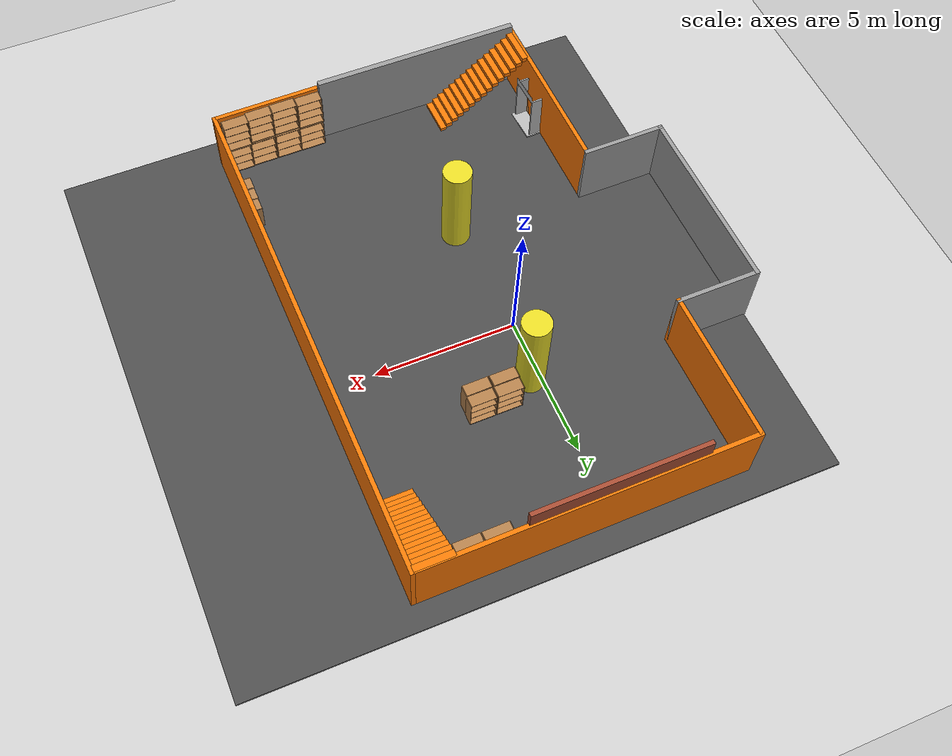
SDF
<sdf version="1.6">
 <world name="default">
  <light name="sun" type="directional">
   <pose>0 0 10 0 -0 0</pose>
   <diffuse>0.8 0.8 0.8 1</diffuse>
   <specular>0.2 0.2 0.2 1</specular>
   <attenuation>
    <range>1000</range>
    <constant>0.9</constant>
    <linear>0.01</linear>
    <quadratic>0.001</quadratic>
   </attenuation>
   <direction>-0.5 0.1 -0.9</direction>
  </light>
  <model name="ground_plane">
   <static>1</static>
   <link name="link">
    <collision name="collision">
     <geometry><plane><normal>0 0 1</normal><size>100 100</size></plane></geometry>
     <surface>
      <contact><collide_bitmask>65535</collide_bitmask></contact>
      <friction><ode><mu>100</mu><mu2>50</mu2></ode></friction>
     </surface>
    </collision>
    <visual name="visual">
     <cast_shadows>0</cast_shadows>
     <geometry><plane><normal>0 0 1</normal><size>100 100</size></plane></geometry>
     <material>
      <script><uri>file://media/materials/scripts/gazebo.material</uri><name>Gazebo/Grey</name></script>
     </material>
    </visual>
   </link>
  </model>
  <gravity>0 0 -9.8</gravity>
  <magnetic_field>6e-06 2.3e-05 -4.2e-05</magnetic_field>
  <atmosphere type="adiabatic"/>
  <physics name="default_physics" default="0" type="ode">
   <max_step_size>0.001</max_step_size>
   <real_time_factor>1</real_time_factor>
   <real_time_update_rate>1000</real_time_update_rate>
  </physics>
  <scene><ambient>0.4 0.4 0.4 1</ambient><background>0.7 0.7 0.7 1</background><shadows>1</shadows></scene>
  <spherical_coordinates>
   <surface_model>EARTH_WGS84</surface_model>
   <latitude_deg>0</latitude_deg>
   <longitude_deg>0</longitude_deg>
   <elevation>0</elevation>
   <heading_deg>0</heading_deg>
  </spherical_coordinates>
  <model name="room">
   <pose>-0.243156 -1.3901 0 0 0 -1.56463</pose>
   <link name="Wall_0">
    <collision name="Wall_0_Collision">
     <geometry><box><size>3 0.15 2.5</size></box></geometry>
     <pose>0 0 1.25 0 -0 0</pose>
    </collision>
    <visual name="Wall_0_Visual">
     <pose>0 0 1.25 0 -0 0</pose>
     <geometry><box><size>3 0.15 2.5</size></box></geometry>
     <material>
      <script><uri>file://media/materials/scripts/gazebo.material</uri><name>Gazebo/Grey</name></script>
      <ambient>1 1 1 1</ambient>
     </material>
     <meta><layer>0</layer></meta>
    </visual>
    <pose>-3.9 -5.675 0 0 -0 -1.5708</pose>
   </link>
   <link name="Wall_1">
    <collision name="Wall_1_Collision">
     <geometry><box><size>6.75 0.15 2.5</size></box></geometry>
     <pose>0 0 1.25 0 -0 0</pose>
    </collision>
    <visual name="Wall_1_Visual">
     <pose>0 0 1.25 0 -0 0</pose>
     <geometry><box><size>6.75 0.15 2.5</size></box></geometry>
     <material>
      <script><uri>file://media/materials/scripts/gazebo.material</uri><name>Gazebo/Grey</name></script>
      <ambient>1 1 1 1</ambient>
     </material>
     <meta><layer>0</layer></meta>
    </visual>
    <pose>-0.6 -7.1 0 0 -0 0</pose>
   </link>
   <link name="Wall_2">
    <collision name="Wall_2_Collision">
     <geometry><box><size>3 0.15 2.5</size></box></geometry>
     <pose>0 0 1.25 0 -0 0</pose>
    </collision>
    <visual name="Wall_2_Visual">
     <pose>0 0 1.25 0 -0 0</pose>
     <geometry><box><size>3 0.15 2.5</size></box></geometry>
     <material>
      <script><uri>file://media/materials/scripts/gazebo.material</uri><name>Gazebo/Grey</name></script>
      <ambient>1 1 1 1</ambient>
     </material>
     <meta><layer>0</layer></meta>
    </visual>
    <pose>2.7 -5.675 0 0 -0 1.5708</pose>
   </link>
   <link name="Wall_3">
    <collision name="Wall_3_Collision">
     <geometry><box><size>6.5 0.15 2.5</size></box></geometry>
     <pose>0 0 1.25 0 -0 0</pose>
    </collision>
    <visual name="Wall_3_Visual">
     <pose>0 0 1.25 0 -0 0</pose>
     <geometry><box><size>6.5 0.15 2.5</size></box></geometry>
     <material>
      <script><uri>file://media/materials/scripts/gazebo.material</uri><name>Gazebo/Grey</name></script>
      <ambient>0.996078 0.47451 0.0196078 1</ambient>
     </material>
     <meta><layer>0</layer></meta>
    </visual>
    <pose>5.875 -4.25 0 0 -0 0</pose>
   </link>
   <link name="Wall_5">
    <collision name="Wall_5_Collision">
     <geometry><box><size>11.5 0.15 2.5</size></box></geometry>
     <pose>0 0 1.25 0 -0 0</pose>
    </collision>
    <visual name="Wall_5_Visual">
     <pose>0 0 1.25 0 -0 0</pose>
     <geometry><box><size>11.5 0.15 2.5</size></box></geometry>
     <material>
      <script><uri>file://media/materials/scripts/gazebo.material</uri><name>Gazebo/Grey</name></script>
      <ambient>0.996078 0.47451 0.0196078 1</ambient>
     </material>
     <meta><layer>0</layer></meta>
    </visual>
    <pose>9.05 1.425 0 0 -0 1.5708</pose>
   </link>
   <link name="Wall_6">
    <collision name="Wall_6_Collision">
     <geometry><box><size>18.25 0.15 2.5</size></box></geometry>
     <pose>0 0 1.25 0 -0 0</pose>
    </collision>
    <visual name="Wall_6_Visual">
     <pose>0 0 1.25 0 -0 0</pose>
     <geometry><box><size>18.25 0.15 2.5</size></box></geometry>
     <material>
      <script><uri>file://media/materials/scripts/gazebo.material</uri><name>Gazebo/Grey</name></script>
      <ambient>0.996078 0.47451 0.0196078 1</ambient>
     </material>
     <meta><layer>0</layer></meta>
    </visual>
    <pose>0 7.1 0 0 -0 3.14159</pose>
   </link>
   <link name="Wall_7">
    <collision name="Wall_7_Collision">
     <geometry><box><size>11.5 0.15 2.5</size></box></geometry>
     <pose>0 0 1.25 0 -0 0</pose>
    </collision>
    <visual name="Wall_7_Visual">
     <pose>0 0 1.25 0 -0 0</pose>
     <geometry><box><size>11.5 0.15 2.5</size></box></geometry>
     <material>
      <script><uri>file://media/materials/scripts/gazebo.material</uri><name>Gazebo/Grey</name></script>
      <ambient>0.996078 0.47451 0.0196078 1</ambient>
     </material>
     <meta><layer>0</layer></meta>
    </visual>
    <pose>-9.05 1.425 0 0 -0 -1.5708</pose>
   </link>
   <link name="Wall_8">
    <collision name="Wall_8_Collision">
     <geometry><box><size>5.3 0.15 2.5</size></box></geometry>
     <pose>0 0 1.25 0 -0 0</pose>
    </collision>
    <visual name="Wall_8_Visual">
     <pose>0 0 1.25 0 -0 0</pose>
     <geometry><box><size>5.3 0.15 2.5</size></box></geometry>
     <material>
      <script><uri>file://media/materials/scripts/gazebo.material</uri><name>Gazebo/Grey</name></script>
      <ambient>0.996078 0.47451 0.0196078 1</ambient>
     </material>
     <meta><layer>0</layer></meta>
    </visual>
    <pose>-6.475 -4.25 0 0 -0 0</pose>
   </link>
   <static>1</static>
  </model>
  <model name="wall_with_num">
   <pose>0.139426 7.61579 1.58041 -0.028957 -0.000253 -3.13441</pose>
   <static>1</static>
   <link name="wall_link">
    <inertial><mass>1</mass></inertial>
    <collision name="my_collision"><geometry><box><size>6 0.15 3</size></box></geometry></collision>
    <visual name="my_visual">
     <geometry><box><size>6 0.15 3</size></box></geometry>
     <material>
      <script><uri>file://media/materials/scripts/gazebo.material</uri><name>Gazebo/Bricks</name></script>
      <ambient>1 1 1 1</ambient>
     </material>
    </visual>
   </link>
   <link name="logo">
    <pose>-0 0.07 -0 0 -0 0</pose>
    <collision name="collision"><geometry><box><size>0.5 0.01 0.5</size></box></geometry></collision>
    <visual name="visual">
     <cast_shadows>0</cast_shadows>
     <geometry><box><size>4.5 0.03 1</size></box></geometry>
     <material>
      <script>
       <uri>model://logo_ground/materials/scripts</uri>
       <uri>model://logo_ground/materials/textures</uri>
       <name>Cube/logo_ground</name>
      </script>
     </material>
    </visual>
   </link>
   <link name="num_0">
    <pose>2 0.07 1 0 -0 0</pose>
    <collision name="collision"><geometry><box><size>0.5 0.01 0.5</size></box></geometry></collision>
    <visual name="visual">
     <cast_shadows>0</cast_shadows>
     <geometry><box><size>0.5 0.03 0.5</size></box></geometry>
     <material>
      <script>
       <uri>model://wall_with_num/materials/scripts/numbers.material</uri>
       <uri>model://wall_with_num/materials/textures/</uri>
       <name>Numbers/0</name>
      </script>
     </material>
    </visual>
   </link>
   <link name="num_1">
    <pose>1 0.07 1 0 -0 0</pose>
    <collision name="collision"><geometry><box><size>0.5 0.01 0.5</size></box></geometry></collision>
    <visual name="visual">
     <cast_shadows>0</cast_shadows>
     <geometry><box><size>0.5 0.03 0.5</size></box></geometry>
     <material>
      <script>
       <uri>model://wall_with_num/materials/scripts/numbers.material</uri>
       <uri>model://wall_with_num/materials/textures/</uri>
       <name>Numbers/1</name>
      </script>
     </material>
    </visual>
   </link>
   <link name="num_2">
    <pose>0 0.07 1 0 -0 0</pose>
    <collision name="collision"><geometry><box><size>0.5 0.01 0.5</size></box></geometry></collision>
    <visual name="visual">
     <cast_shadows>0</cast_shadows>
     <geometry><box><size>0.5 0.03 0.5</size></box></geometry>
     <material>
      <script>
       <uri>model://wall_with_num/materials/scripts/numbers.material</uri>
       <uri>model://wall_with_num/materials/textures/</uri>
       <name>Numbers/2</name>
      </script>
     </material>
    </visual>
   </link>
   <link name="num_3">
    <pose>-1 0.07 1 0 -0 0</pose>
    <collision name="collision"><geometry><box><size>0.5 0.01 0.5</size></box></geometry></collision>
    <visual name="visual">
     <cast_shadows>0</cast_shadows>
     <geometry><box><size>0.5 0.03 0.5</size></box></geometry>
     <material>
      <script>
       <uri>model://wall_with_num/materials/scripts/numbers.material</uri>
       <uri>model://wall_with_num/materials/textures/</uri>
       <name>Numbers/3</name>
      </script>
     </material>
    </visual>
   </link>
   <link name="num_4">
    <pose>-2 0.07 1 0 -0 0</pose>
    <collision name="collision"><geometry><box><size>0.5 0.01 0.5</size></box></geometry></collision>
    <visual name="visual">
     <cast_shadows>0</cast_shadows>
     <geometry><box><size>0.5 0.03 0.5</size></box></geometry>
     <material>
      <script>
       <uri>model://wall_with_num/materials/scripts/numbers.material</uri>
       <uri>model://wall_with_num/materials/textures/</uri>
       <name>Numbers/4</name>
      </script>
     </material>
    </visual>
   </link>
   <link name="num_5">
    <pose>2 0.07 -1 0 -0 0</pose>
    <collision name="collision"><geometry><box><size>0.5 0.01 0.5</size></box></geometry></collision>
    <visual name="visual">
     <cast_shadows>0</cast_shadows>
     <geometry><box><size>0.5 0.03 0.5</size></box></geometry>
     <material>
      <script>
       <uri>model://wall_with_num/materials/scripts/numbers.material</uri>
       <uri>model://wall_with_num/materials/textures/</uri>
       <name>Numbers/5</name>
      </script>
     </material>
    </visual>
   </link>
   <link name="num_6">
    <pose>1 0.07 -1 0 -0 0</pose>
    <collision name="collision"><geometry><box><size>0.5 0.01 0.5</size></box></geometry></collision>
    <visual name="visual">
     <cast_shadows>0</cast_shadows>
     <geometry><box><size>0.5 0.03 0.5</size></box></geometry>
     <material>
      <script>
       <uri>model://wall_with_num/materials/scripts/numbers.material</uri>
       <uri>model://wall_with_num/materials/textures/</uri>
       <name>Numbers/6</name>
      </script>
     </material>
    </visual>
   </link>
   <link name="num_7">
    <pose>0 0.07 -1 0 -0 0</pose>
    <collision name="collision"><geometry><box><size>0.5 0.01 0.5</size></box></geometry></collision>
    <visual name="visual">
     <cast_shadows>0</cast_shadows>
     <geometry><box><size>0.5 0.03 0.5</size></box></geometry>
     <material>
      <script>
       <uri>model://wall_with_num/materials/scripts/numbers.material</uri>
       <uri>model://wall_with_num/materials/textures/</uri>
       <name>Numbers/7</name>
      </script>
     </material>
    </visual>
   </link>
   <link name="num_8">
    <pose>-1 0.07 -1 0 -0 0</pose>
    <collision name="collision"><geometry><box><size>0.5 0.01 0.5</size></box></geometry></collision>
    <visual name="visual">
     <cast_shadows>0</cast_shadows>
     <geometry><box><size>0.5 0.03 0.5</size></box></geometry>
     <material>
      <script>
       <uri>model://wall_with_num/materials/scripts/numbers.material</uri>
       <uri>model://wall_with_num/materials/textures/</uri>
       <name>Numbers/8</name>
      </script>
     </material>
    </visual>
   </link>
   <link name="num_9">
    <pose>-2 0.07 -1 0 -0 0</pose>
    <collision name="collision"><geometry><box><size>0.5 0.01 0.5</size></box></geometry></collision>
    <visual name="visual">
     <cast_shadows>0</cast_shadows>
     <geometry><box><size>0.5 0.03 0.5</size></box></geometry>
     <material>
      <script>
       <uri>model://wall_with_num/materials/scripts/numbers.material</uri>
       <uri>model://wall_with_num/materials/textures/</uri>
       <name>Numbers/9</name>
      </script>
     </material>
    </visual>
   </link>
  </model>
  <model name="stone_10_2_5_1cm">
   <link name="link">
    <pose>0 0 0.005 0 -0 0</pose>
    <inertial>
     <mass>0.0628</mass>
     <inertia>
      <ixx>3.79417e-06</ixx>
      <ixy>0</ixy>
      <ixz>0</ixz>
      <iyy>5.28567e-05</iyy>
      <iyz>0</iyz>
      <izz>5.56042e-05</izz>
     </inertia>
    </inertial>
    <collision name="collision">
     <geometry><box><size>0.1 0.025 0.01</size></box></geometry>
     <surface>
      <contact>
       <poissons_ratio>0.15</poissons_ratio>
       <elastic_modulus>8e+10</elastic_modulus>
       <ode><kp>100000</kp><kd>100</kd><max_vel>100</max_vel><min_depth>0.001</min_depth></ode>
      </contact>
      <friction>
       <torsional>
        <coefficient>1</coefficient>
        <use_patch_radius>0</use_patch_radius>
        <surface_radius>0.01</surface_radius>
       </torsional>
      </friction>
     </surface>
    </collision>
    <visual name="visual">
     <geometry><box><size>0.1 0.025 0.01</size></box></geometry>
     <material>
      <script><uri>file://media/materials/scripts/gazebo.material</uri><name>Gazebo/Grey</name></script>
     </material>
    </visual>
   </link>
   <pose>0 0 -0.005 0 -0 0</pose>
  </model>
  <plugin name="ros_interface_plugin" filename="librotors_gazebo_ros_interface_plugin.so"/>
  <model name="frc2016_drawbridge">
   <link name="base">
    <inertial>
     <mass>10</mass>
     <pose>0 0 1 0 -0 0</pose>
     <inertia><ixx>3.64907</ixx><ixy>0</ixy><ixz>0</ixz><iyy>4.67075</iyy><iyz>0</iyz><izz>1.66649</izz></inertia>
    </inertial>
    <visual name="platform">
     <pose>0 0 0.0425 0 -0 0</pose>
     <geometry><box><size>1.27 0.5969 0.085</size></box></geometry>
    </visual>
    <collision name="platform">
     <pose>0 0 0.0425 0 -0 0</pose>
     <geometry><box><size>1.27 0.5969 0.085</size></box></geometry>
    </collision>
    <visual name="right_wall">
     <pose>0.55879 0.04444 0.889 0 -0 0</pose>
     <geometry><box><size>0.05715 0.45698 1.77165</size></box></geometry>
    </visual>
    <collision name="right_wall">
     <pose>0.55879 0.04444 0.889 0 -0 0</pose>
     <geometry><box><size>0.05715 0.45698 1.77165</size></box></geometry>
    </collision>
    <visual name="left_wall">
     <pose>-0.55879 0.04444 0.889 0 -0 0</pose>
     <geometry><box><size>0.05715 0.45698 1.77165</size></box></geometry>
    </visual>
    <collision name="left_wall">
     <pose>-0.55879 0.04444 0.889 0 -0 0</pose>
     <geometry><box><size>0.05715 0.45698 1.77165</size></box></geometry>
    </collision>
    <visual name="front_upper_wall">
     <pose>0 0.27611 1.84286 0 -0 0</pose>
     <geometry><box><size>1.1557 0.006347 0.254</size></box></geometry>
    </visual>
    <collision name="front_upper_wall">
     <pose>0 0.27611 1.84286 0 -0 0</pose>
     <geometry><box><size>1.1557 0.006347 0.254</size></box></geometry>
    </collision>
    <visual name="back_upper_wall">
     <pose>0 -0.18722 1.84286 0 -0 0</pose>
     <geometry><box><size>1.1557 0.006347 0.254</size></box></geometry>
    </visual>
    <collision name="back_upper_wall">
     <pose>0 -0.18722 1.84286 0 -0 0</pose>
     <geometry><box><size>1.1557 0.006347 0.254</size></box></geometry>
    </collision>
   </link>
   <link name="bridge">
    <pose>0 0.28245 0.50577 0 -0 0</pose>
    <inertial>
     <mass>2</mass>
     <pose>0 -0.28245 -0.50577 0 -0 0</pose>
     <inertia>
      <ixx>0.139361</ixx>
      <ixy>0</ixy>
      <ixz>0</ixz>
      <iyy>0.357088</iyy>
      <iyz>0</iyz>
      <izz>0.217741</izz>
     </inertia>
    </inertial>
    <visual name="visual">
     <geometry><box><size>1.14298 0.006347 0.9144</size></box></geometry>
     <material><script><name>Gazebo/WoodFloor</name><uri>__default__</uri></script></material>
    </visual>
    <collision name="collision"><geometry><box><size>1.14298 0.006347 0.9144</size></box></geometry></collision>
   </link>
   <joint name="bridge_joint" type="revolute">
    <pose>0 0 -0.4172 0 -0 0</pose>
    <parent>base</parent>
    <child>bridge</child>
    <axis>
     <xyz>1 0 0</xyz>
     <limit><lower>-2</lower><upper>0</upper></limit>
     <use_parent_model_frame>0</use_parent_model_frame>
     <dynamics><spring_reference>0</spring_reference><spring_stiffness>0</spring_stiffness></dynamics>
    </axis>
   </joint>
   <pose>-4.11079 -7.91679 0 -0.010755 -0.031899 1.61279</pose>
  </model>
  <model name="bookshelf">
   <static>1</static>
   <link name="link">
    <inertial><mass>1</mass></inertial>
    <collision name="back">
     <pose>0 0.005 0.6 0 -0 0</pose>
     <geometry><box><size>0.9 0.01 1.2</size></box></geometry>
    </collision>
    <visual name="visual1">
     <pose>0 0.005 0.6 0 -0 0</pose>
     <geometry><box><size>0.9 0.01 1.2</size></box></geometry>
     <material>
      <script><uri>file://media/materials/scripts/gazebo.material</uri><name>Gazebo/Wood</name></script>
     </material>
    </visual>
    <collision name="left_side">
     <pose>0.45 -0.195 0.6 0 -0 0</pose>
     <geometry><box><size>0.02 0.4 1.2</size></box></geometry>
    </collision>
    <visual name="visual2">
     <pose>0.45 -0.195 0.6 0 -0 0</pose>
     <geometry><box><size>0.02 0.4 1.2</size></box></geometry>
     <material>
      <script><uri>file://media/materials/scripts/gazebo.material</uri><name>Gazebo/Wood</name></script>
     </material>
    </visual>
    <collision name="right_side">
     <pose>-0.45 -0.195 0.6 0 -0 0</pose>
     <geometry><box><size>0.02 0.4 1.2</size></box></geometry>
    </collision>
    <visual name="visual3">
     <pose>-0.45 -0.195 0.6 0 -0 0</pose>
     <geometry><box><size>0.02 0.4 1.2</size></box></geometry>
     <material>
      <script><uri>file://media/materials/scripts/gazebo.material</uri><name>Gazebo/Wood</name></script>
     </material>
    </visual>
    <collision name="bottom">
     <pose>0 -0.195 0.03 0 -0 0</pose>
     <geometry><box><size>0.88 0.4 0.06</size></box></geometry>
    </collision>
    <visual name="visual4">
     <pose>0 -0.195 0.03 0 -0 0</pose>
     <geometry><box><size>0.88 0.4 0.06</size></box></geometry>
     <material>
      <script><uri>file://media/materials/scripts/gazebo.material</uri><name>Gazebo/Wood</name></script>
     </material>
    </visual>
    <collision name="top">
     <pose>0 -0.195 1.19 0 -0 0</pose>
     <geometry><box><size>0.88 0.4 0.02</size></box></geometry>
    </collision>
    <visual name="visual5">
     <pose>0 -0.195 1.19 0 -0 0</pose>
     <geometry><box><size>0.88 0.4 0.02</size></box></geometry>
     <material>
      <script><uri>file://media/materials/scripts/gazebo.material</uri><name>Gazebo/Wood</name></script>
     </material>
    </visual>
    <collision name="low_shelf">
     <pose>0 -0.195 0.43 0 -0 0</pose>
     <geometry><box><size>0.88 0.4 0.02</size></box></geometry>
    </collision>
    <visual name="visual6">
     <pose>0 -0.195 0.43 0 -0 0</pose>
     <geometry><box><size>0.88 0.4 0.02</size></box></geometry>
     <material>
      <script><uri>file://media/materials/scripts/gazebo.material</uri><name>Gazebo/Wood</name></script>
     </material>
    </visual>
    <collision name="high_shelf">
     <pose>0 -0.195 0.8 0 -0 0</pose>
     <geometry><box><size>0.88 0.4 0.02</size></box></geometry>
    </collision>
    <visual name="visual7">
     <pose>0 -0.195 0.8 0 -0 0</pose>
     <geometry><box><size>0.88 0.4 0.02</size></box></geometry>
     <material>
      <script><uri>file://media/materials/scripts/gazebo.material</uri><name>Gazebo/Wood</name></script>
     </material>
    </visual>
   </link>
   <pose>6.34692 -10.2259 0.027497 0 0 -3.13702</pose>
  </model>
  <model name="bookshelf_clone">
   <static>1</static>
   <link name="link">
    <inertial><mass>1</mass></inertial>
    <collision name="back">
     <pose>0 0.005 0.6 0 -0 0</pose>
     <geometry><box><size>0.9 0.01 1.2</size></box></geometry>
    </collision>
    <visual name="visual1">
     <pose>0 0.005 0.6 0 -0 0</pose>
     <geometry><box><size>0.9 0.01 1.2</size></box></geometry>
     <material>
      <script><uri>file://media/materials/scripts/gazebo.material</uri><name>Gazebo/Wood</name></script>
     </material>
    </visual>
    <collision name="left_side">
     <pose>0.45 -0.195 0.6 0 -0 0</pose>
     <geometry><box><size>0.02 0.4 1.2</size></box></geometry>
    </collision>
    <visual name="visual2">
     <pose>0.45 -0.195 0.6 0 -0 0</pose>
     <geometry><box><size>0.02 0.4 1.2</size></box></geometry>
     <material>
      <script><uri>file://media/materials/scripts/gazebo.material</uri><name>Gazebo/Wood</name></script>
     </material>
    </visual>
    <collision name="right_side">
     <pose>-0.45 -0.195 0.6 0 -0 0</pose>
     <geometry><box><size>0.02 0.4 1.2</size></box></geometry>
    </collision>
    <visual name="visual3">
     <pose>-0.45 -0.195 0.6 0 -0 0</pose>
     <geometry><box><size>0.02 0.4 1.2</size></box></geometry>
     <material>
      <script><uri>file://media/materials/scripts/gazebo.material</uri><name>Gazebo/Wood</name></script>
     </material>
    </visual>
    <collision name="bottom">
     <pose>0 -0.195 0.03 0 -0 0</pose>
     <geometry><box><size>0.88 0.4 0.06</size></box></geometry>
    </collision>
    <visual name="visual4">
     <pose>0 -0.195 0.03 0 -0 0</pose>
     <geometry><box><size>0.88 0.4 0.06</size></box></geometry>
     <material>
      <script><uri>file://media/materials/scripts/gazebo.material</uri><name>Gazebo/Wood</name></script>
     </material>
    </visual>
    <collision name="top">
     <pose>0 -0.195 1.19 0 -0 0</pose>
     <geometry><box><size>0.88 0.4 0.02</size></box></geometry>
    </collision>
    <visual name="visual5">
     <pose>0 -0.195 1.19 0 -0 0</pose>
     <geometry><box><size>0.88 0.4 0.02</size></box></geometry>
     <material>
      <script><uri>file://media/materials/scripts/gazebo.material</uri><name>Gazebo/Wood</name></script>
     </material>
    </visual>
    <collision name="low_shelf">
     <pose>0 -0.195 0.43 0 -0 0</pose>
     <geometry><box><size>0.88 0.4 0.02</size></box></geometry>
    </collision>
    <visual name="visual6">
     <pose>0 -0.195 0.43 0 -0 0</pose>
     <geometry><box><size>0.88 0.4 0.02</size></box></geometry>
     <material>
      <script><uri>file://media/materials/scripts/gazebo.material</uri><name>Gazebo/Wood</name></script>
     </material>
    </visual>
    <collision name="high_shelf">
     <pose>0 -0.195 0.8 0 -0 0</pose>
     <geometry><box><size>0.88 0.4 0.02</size></box></geometry>
    </collision>
    <visual name="visual7">
     <pose>0 -0.195 0.8 0 -0 0</pose>
     <geometry><box><size>0.88 0.4 0.02</size></box></geometry>
     <material>
      <script><uri>file://media/materials/scripts/gazebo.material</uri><name>Gazebo/Wood</name></script>
     </material>
    </visual>
   </link>
   <pose>5.43755 -10.2582 0.027497 0 0 -3.13702</pose>
  </model>
  <model name="bookshelf_clone_clone">
   <static>1</static>
   <link name="link">
    <inertial><mass>1</mass></inertial>
    <collision name="back">
     <pose>0 0.005 0.6 0 -0 0</pose>
     <geometry><box><size>0.9 0.01 1.2</size></box></geometry>
    </collision>
    <visual name="visual1">
     <pose>0 0.005 0.6 0 -0 0</pose>
     <geometry><box><size>0.9 0.01 1.2</size></box></geometry>
     <material>
      <script><uri>file://media/materials/scripts/gazebo.material</uri><name>Gazebo/Wood</name></script>
     </material>
    </visual>
    <collision name="left_side">
     <pose>0.45 -0.195 0.6 0 -0 0</pose>
     <geometry><box><size>0.02 0.4 1.2</size></box></geometry>
    </collision>
    <visual name="visual2">
     <pose>0.45 -0.195 0.6 0 -0 0</pose>
     <geometry><box><size>0.02 0.4 1.2</size></box></geometry>
     <material>
      <script><uri>file://media/materials/scripts/gazebo.material</uri><name>Gazebo/Wood</name></script>
     </material>
    </visual>
    <collision name="right_side">
     <pose>-0.45 -0.195 0.6 0 -0 0</pose>
     <geometry><box><size>0.02 0.4 1.2</size></box></geometry>
    </collision>
    <visual name="visual3">
     <pose>-0.45 -0.195 0.6 0 -0 0</pose>
     <geometry><box><size>0.02 0.4 1.2</size></box></geometry>
     <material>
      <script><uri>file://media/materials/scripts/gazebo.material</uri><name>Gazebo/Wood</name></script>
     </material>
    </visual>
    <collision name="bottom">
     <pose>0 -0.195 0.03 0 -0 0</pose>
     <geometry><box><size>0.88 0.4 0.06</size></box></geometry>
    </collision>
    <visual name="visual4">
     <pose>0 -0.195 0.03 0 -0 0</pose>
     <geometry><box><size>0.88 0.4 0.06</size></box></geometry>
     <material>
      <script><uri>file://media/materials/scripts/gazebo.material</uri><name>Gazebo/Wood</name></script>
     </material>
    </visual>
    <collision name="top">
     <pose>0 -0.195 1.19 0 -0 0</pose>
     <geometry><box><size>0.88 0.4 0.02</size></box></geometry>
    </collision>
    <visual name="visual5">
     <pose>0 -0.195 1.19 0 -0 0</pose>
     <geometry><box><size>0.88 0.4 0.02</size></box></geometry>
     <material>
      <script><uri>file://media/materials/scripts/gazebo.material</uri><name>Gazebo/Wood</name></script>
     </material>
    </visual>
    <collision name="low_shelf">
     <pose>0 -0.195 0.43 0 -0 0</pose>
     <geometry><box><size>0.88 0.4 0.02</size></box></geometry>
    </collision>
    <visual name="visual6">
     <pose>0 -0.195 0.43 0 -0 0</pose>
     <geometry><box><size>0.88 0.4 0.02</size></box></geometry>
     <material>
      <script><uri>file://media/materials/scripts/gazebo.material</uri><name>Gazebo/Wood</name></script>
     </material>
    </visual>
    <collision name="high_shelf">
     <pose>0 -0.195 0.8 0 -0 0</pose>
     <geometry><box><size>0.88 0.4 0.02</size></box></geometry>
    </collision>
    <visual name="visual7">
     <pose>0 -0.195 0.8 0 -0 0</pose>
     <geometry><box><size>0.88 0.4 0.02</size></box></geometry>
     <material>
      <script><uri>file://media/materials/scripts/gazebo.material</uri><name>Gazebo/Wood</name></script>
     </material>
    </visual>
   </link>
   <pose>4.50546 -10.2639 0.027497 0 0 -3.13702</pose>
  </model>
  <model name="bookshelf_clone_clone_0">
   <static>1</static>
   <link name="link">
    <inertial><mass>1</mass></inertial>
    <collision name="back">
     <pose>0 0.005 0.6 0 -0 0</pose>
     <geometry><box><size>0.9 0.01 1.2</size></box></geometry>
    </collision>
    <visual name="visual1">
     <pose>0 0.005 0.6 0 -0 0</pose>
     <geometry><box><size>0.9 0.01 1.2</size></box></geometry>
     <material>
      <script><uri>file://media/materials/scripts/gazebo.material</uri><name>Gazebo/Wood</name></script>
     </material>
    </visual>
    <collision name="left_side">
     <pose>0.45 -0.195 0.6 0 -0 0</pose>
     <geometry><box><size>0.02 0.4 1.2</size></box></geometry>
    </collision>
    <visual name="visual2">
     <pose>0.45 -0.195 0.6 0 -0 0</pose>
     <geometry><box><size>0.02 0.4 1.2</size></box></geometry>
     <material>
      <script><uri>file://media/materials/scripts/gazebo.material</uri><name>Gazebo/Wood</name></script>
     </material>
    </visual>
    <collision name="right_side">
     <pose>-0.45 -0.195 0.6 0 -0 0</pose>
     <geometry><box><size>0.02 0.4 1.2</size></box></geometry>
    </collision>
    <visual name="visual3">
     <pose>-0.45 -0.195 0.6 0 -0 0</pose>
     <geometry><box><size>0.02 0.4 1.2</size></box></geometry>
     <material>
      <script><uri>file://media/materials/scripts/gazebo.material</uri><name>Gazebo/Wood</name></script>
     </material>
    </visual>
    <collision name="bottom">
     <pose>0 -0.195 0.03 0 -0 0</pose>
     <geometry><box><size>0.88 0.4 0.06</size></box></geometry>
    </collision>
    <visual name="visual4">
     <pose>0 -0.195 0.03 0 -0 0</pose>
     <geometry><box><size>0.88 0.4 0.06</size></box></geometry>
     <material>
      <script><uri>file://media/materials/scripts/gazebo.material</uri><name>Gazebo/Wood</name></script>
     </material>
    </visual>
    <collision name="top">
     <pose>0 -0.195 1.19 0 -0 0</pose>
     <geometry><box><size>0.88 0.4 0.02</size></box></geometry>
    </collision>
    <visual name="visual5">
     <pose>0 -0.195 1.19 0 -0 0</pose>
     <geometry><box><size>0.88 0.4 0.02</size></box></geometry>
     <material>
      <script><uri>file://media/materials/scripts/gazebo.material</uri><name>Gazebo/Wood</name></script>
     </material>
    </visual>
    <collision name="low_shelf">
     <pose>0 -0.195 0.43 0 -0 0</pose>
     <geometry><box><size>0.88 0.4 0.02</size></box></geometry>
    </collision>
    <visual name="visual6">
     <pose>0 -0.195 0.43 0 -0 0</pose>
     <geometry><box><size>0.88 0.4 0.02</size></box></geometry>
     <material>
      <script><uri>file://media/materials/scripts/gazebo.material</uri><name>Gazebo/Wood</name></script>
     </material>
    </visual>
    <collision name="high_shelf">
     <pose>0 -0.195 0.8 0 -0 0</pose>
     <geometry><box><size>0.88 0.4 0.02</size></box></geometry>
    </collision>
    <visual name="visual7">
     <pose>0 -0.195 0.8 0 -0 0</pose>
     <geometry><box><size>0.88 0.4 0.02</size></box></geometry>
     <material>
      <script><uri>file://media/materials/scripts/gazebo.material</uri><name>Gazebo/Wood</name></script>
     </material>
    </visual>
   </link>
   <pose>3.59893 -10.2632 0.027497 0 0 -3.13702</pose>
  </model>
  <model name="bookshelf_clone_clone_1">
   <static>1</static>
   <link name="link">
    <inertial><mass>1</mass></inertial>
    <collision name="back">
     <pose>0 0.005 0.6 0 -0 0</pose>
     <geometry><box><size>0.9 0.01 1.2</size></box></geometry>
    </collision>
    <visual name="visual1">
     <pose>0 0.005 0.6 0 -0 0</pose>
     <geometry><box><size>0.9 0.01 1.2</size></box></geometry>
     <material>
      <script><uri>file://media/materials/scripts/gazebo.material</uri><name>Gazebo/Wood</name></script>
     </material>
    </visual>
    <collision name="left_side">
     <pose>0.45 -0.195 0.6 0 -0 0</pose>
     <geometry><box><size>0.02 0.4 1.2</size></box></geometry>
    </collision>
    <visual name="visual2">
     <pose>0.45 -0.195 0.6 0 -0 0</pose>
     <geometry><box><size>0.02 0.4 1.2</size></box></geometry>
     <material>
      <script><uri>file://media/materials/scripts/gazebo.material</uri><name>Gazebo/Wood</name></script>
     </material>
    </visual>
    <collision name="right_side">
     <pose>-0.45 -0.195 0.6 0 -0 0</pose>
     <geometry><box><size>0.02 0.4 1.2</size></box></geometry>
    </collision>
    <visual name="visual3">
     <pose>-0.45 -0.195 0.6 0 -0 0</pose>
     <geometry><box><size>0.02 0.4 1.2</size></box></geometry>
     <material>
      <script><uri>file://media/materials/scripts/gazebo.material</uri><name>Gazebo/Wood</name></script>
     </material>
    </visual>
    <collision name="bottom">
     <pose>0 -0.195 0.03 0 -0 0</pose>
     <geometry><box><size>0.88 0.4 0.06</size></box></geometry>
    </collision>
    <visual name="visual4">
     <pose>0 -0.195 0.03 0 -0 0</pose>
     <geometry><box><size>0.88 0.4 0.06</size></box></geometry>
     <material>
      <script><uri>file://media/materials/scripts/gazebo.material</uri><name>Gazebo/Wood</name></script>
     </material>
    </visual>
    <collision name="top">
     <pose>0 -0.195 1.19 0 -0 0</pose>
     <geometry><box><size>0.88 0.4 0.02</size></box></geometry>
    </collision>
    <visual name="visual5">
     <pose>0 -0.195 1.19 0 -0 0</pose>
     <geometry><box><size>0.88 0.4 0.02</size></box></geometry>
     <material>
      <script><uri>file://media/materials/scripts/gazebo.material</uri><name>Gazebo/Wood</name></script>
     </material>
    </visual>
    <collision name="low_shelf">
     <pose>0 -0.195 0.43 0 -0 0</pose>
     <geometry><box><size>0.88 0.4 0.02</size></box></geometry>
    </collision>
    <visual name="visual6">
     <pose>0 -0.195 0.43 0 -0 0</pose>
     <geometry><box><size>0.88 0.4 0.02</size></box></geometry>
     <material>
      <script><uri>file://media/materials/scripts/gazebo.material</uri><name>Gazebo/Wood</name></script>
     </material>
    </visual>
    <collision name="high_shelf">
     <pose>0 -0.195 0.8 0 -0 0</pose>
     <geometry><box><size>0.88 0.4 0.02</size></box></geometry>
    </collision>
    <visual name="visual7">
     <pose>0 -0.195 0.8 0 -0 0</pose>
     <geometry><box><size>0.88 0.4 0.02</size></box></geometry>
     <material>
      <script><uri>file://media/materials/scripts/gazebo.material</uri><name>Gazebo/Wood</name></script>
     </material>
    </visual>
   </link>
   <pose>-4.0173 7.67055 0.027497 0 0 -0.028777</pose>
  </model>
  <model name="cabinet_clone_1">
   <static>1</static>
   <link name="cabinet_bottom_plate">
    <inertial>
     <pose>0 0 -1 0 -0 0</pose>
     <inertia><ixx>2.05</ixx><ixy>0</ixy><ixz>0</ixz><iyy>2.05</iyy><iyz>0</iyz><izz>2.05</izz></inertia>
     <mass>25</mass>
    </inertial>
    <collision name="cabinet_bottom_plate_geom">
     <pose>0 0 0.01 0 -0 0</pose>
     <geometry><box><size>0.45 0.45 0.02</size></box></geometry>
    </collision>
    <visual name="cabinet_bottom_plate_geom_visual">
     <pose>0 0 0.01 0 -0 0</pose>
     <geometry><box><size>0.45 0.45 0.02</size></box></geometry>
     <material>
      <script><uri>file://media/materials/scripts/gazebo.material</uri><name>Gazebo/Wood</name></script>
     </material>
    </visual>
    <collision name="cabinet_bottom_plate_geom_cabinet_back_plate">
     <pose>0.235 0 0.51 0 -0 0</pose>
     <geometry><box><size>0.02 0.45 1.02</size></box></geometry>
    </collision>
    <visual name="cabinet_bottom_plate_geom_cabinet_back_plate_visual">
     <pose>0.235 0 0.51 0 -0 0</pose>
     <geometry><box><size>0.02 0.45 1.02</size></box></geometry>
     <material>
      <script><uri>file://media/materials/scripts/gazebo.material</uri><name>Gazebo/Wood</name></script>
     </material>
    </visual>
    <collision name="cabinet_bottom_plate_geom_cabinet_left_plate">
     <pose>0 0.235 0.51 0 -0 0</pose>
     <geometry><box><size>0.45 0.02 1.02</size></box></geometry>
    </collision>
    <visual name="cabinet_bottom_plate_geom_cabinet_left_plate_visual">
     <pose>0 0.235 0.51 0 -0 0</pose>
     <geometry><box><size>0.45 0.02 1.02</size></box></geometry>
     <material>
      <script><uri>file://media/materials/scripts/gazebo.material</uri><name>Gazebo/Wood</name></script>
     </material>
    </visual>
    <collision name="cabinet_bottom_plate_geom_cabinet_middle_plate">
     <pose>0 0 0.51 0 -0 0</pose>
     <geometry><box><size>0.45 0.45 0.02</size></box></geometry>
    </collision>
    <visual name="cabinet_bottom_plate_geom_cabinet_middle_plate_visual">
     <pose>0 0 0.51 0 -0 0</pose>
     <geometry><box><size>0.45 0.45 0.02</size></box></geometry>
     <material>
      <script><uri>file://media/materials/scripts/gazebo.material</uri><name>Gazebo/Wood</name></script>
     </material>
    </visual>
    <collision name="cabinet_bottom_plate_geom_cabinet_right_plate">
     <pose>0 -0.235 0.51 0 -0 0</pose>
     <geometry><box><size>0.45 0.02 1.02</size></box></geometry>
    </collision>
    <visual name="cabinet_bottom_plate_geom_cabinet_right_plate_visual">
     <pose>0 -0.235 0.51 0 -0 0</pose>
     <geometry><box><size>0.45 0.02 1.02</size></box></geometry>
     <material>
      <script><uri>file://media/materials/scripts/gazebo.material</uri><name>Gazebo/Wood</name></script>
     </material>
    </visual>
    <collision name="cabinet_bottom_plate_geom_cabinet_top_plate">
     <pose>0 0 1.01 0 -0 0</pose>
     <geometry><box><size>0.45 0.45 0.02</size></box></geometry>
    </collision>
    <visual name="cabinet_bottom_plate_geom_cabinet_top_plate_visual">
     <pose>0 0 1.01 0 -0 0</pose>
     <geometry><box><size>0.45 0.45 0.02</size></box></geometry>
     <material>
      <script><uri>file://media/materials/scripts/gazebo.material</uri><name>Gazebo/Wood</name></script>
     </material>
    </visual>
   </link>
   <pose>6.62637 -7.40412 0 0 -0 0</pose>
  </model>
  <model name="cabinet_clone_2">
   <static>1</static>
   <link name="cabinet_bottom_plate">
    <inertial>
     <pose>0 0 -1 0 -0 0</pose>
     <inertia><ixx>2.05</ixx><ixy>0</ixy><ixz>0</ixz><iyy>2.05</iyy><iyz>0</iyz><izz>2.05</izz></inertia>
     <mass>25</mass>
    </inertial>
    <collision name="cabinet_bottom_plate_geom">
     <pose>0 0 0.01 0 -0 0</pose>
     <geometry><box><size>0.45 0.45 0.02</size></box></geometry>
    </collision>
    <visual name="cabinet_bottom_plate_geom_visual">
     <pose>0 0 0.01 0 -0 0</pose>
     <geometry><box><size>0.45 0.45 0.02</size></box></geometry>
     <material>
      <script><uri>file://media/materials/scripts/gazebo.material</uri><name>Gazebo/Wood</name></script>
     </material>
    </visual>
    <collision name="cabinet_bottom_plate_geom_cabinet_back_plate">
     <pose>0.235 0 0.51 0 -0 0</pose>
     <geometry><box><size>0.02 0.45 1.02</size></box></geometry>
    </collision>
    <visual name="cabinet_bottom_plate_geom_cabinet_back_plate_visual">
     <pose>0.235 0 0.51 0 -0 0</pose>
     <geometry><box><size>0.02 0.45 1.02</size></box></geometry>
     <material>
      <script><uri>file://media/materials/scripts/gazebo.material</uri><name>Gazebo/Wood</name></script>
     </material>
    </visual>
    <collision name="cabinet_bottom_plate_geom_cabinet_left_plate">
     <pose>0 0.235 0.51 0 -0 0</pose>
     <geometry><box><size>0.45 0.02 1.02</size></box></geometry>
    </collision>
    <visual name="cabinet_bottom_plate_geom_cabinet_left_plate_visual">
     <pose>0 0.235 0.51 0 -0 0</pose>
     <geometry><box><size>0.45 0.02 1.02</size></box></geometry>
     <material>
      <script><uri>file://media/materials/scripts/gazebo.material</uri><name>Gazebo/Wood</name></script>
     </material>
    </visual>
    <collision name="cabinet_bottom_plate_geom_cabinet_middle_plate">
     <pose>0 0 0.51 0 -0 0</pose>
     <geometry><box><size>0.45 0.45 0.02</size></box></geometry>
    </collision>
    <visual name="cabinet_bottom_plate_geom_cabinet_middle_plate_visual">
     <pose>0 0 0.51 0 -0 0</pose>
     <geometry><box><size>0.45 0.45 0.02</size></box></geometry>
     <material>
      <script><uri>file://media/materials/scripts/gazebo.material</uri><name>Gazebo/Wood</name></script>
     </material>
    </visual>
    <collision name="cabinet_bottom_plate_geom_cabinet_right_plate">
     <pose>0 -0.235 0.51 0 -0 0</pose>
     <geometry><box><size>0.45 0.02 1.02</size></box></geometry>
    </collision>
    <visual name="cabinet_bottom_plate_geom_cabinet_right_plate_visual">
     <pose>0 -0.235 0.51 0 -0 0</pose>
     <geometry><box><size>0.45 0.02 1.02</size></box></geometry>
     <material>
      <script><uri>file://media/materials/scripts/gazebo.material</uri><name>Gazebo/Wood</name></script>
     </material>
    </visual>
    <collision name="cabinet_bottom_plate_geom_cabinet_top_plate">
     <pose>0 0 1.01 0 -0 0</pose>
     <geometry><box><size>0.45 0.45 0.02</size></box></geometry>
    </collision>
    <visual name="cabinet_bottom_plate_geom_cabinet_top_plate_visual">
     <pose>0 0 1.01 0 -0 0</pose>
     <geometry><box><size>0.45 0.45 0.02</size></box></geometry>
     <material>
      <script><uri>file://media/materials/scripts/gazebo.material</uri><name>Gazebo/Wood</name></script>
     </material>
    </visual>
   </link>
   <pose>6.60812 -7.89179 0 0 -0 0</pose>
  </model>
  <model name="cabinet_clone_3">
   <static>1</static>
   <link name="cabinet_bottom_plate">
    <inertial>
     <pose>0 0 -1 0 -0 0</pose>
     <inertia><ixx>2.05</ixx><ixy>0</ixy><ixz>0</ixz><iyy>2.05</iyy><iyz>0</iyz><izz>2.05</izz></inertia>
     <mass>25</mass>
    </inertial>
    <collision name="cabinet_bottom_plate_geom">
     <pose>0 0 0.01 0 -0 0</pose>
     <geometry><box><size>0.45 0.45 0.02</size></box></geometry>
    </collision>
    <visual name="cabinet_bottom_plate_geom_visual">
     <pose>0 0 0.01 0 -0 0</pose>
     <geometry><box><size>0.45 0.45 0.02</size></box></geometry>
     <material>
      <script><uri>file://media/materials/scripts/gazebo.material</uri><name>Gazebo/Wood</name></script>
     </material>
    </visual>
    <collision name="cabinet_bottom_plate_geom_cabinet_back_plate">
     <pose>0.235 0 0.51 0 -0 0</pose>
     <geometry><box><size>0.02 0.45 1.02</size></box></geometry>
    </collision>
    <visual name="cabinet_bottom_plate_geom_cabinet_back_plate_visual">
     <pose>0.235 0 0.51 0 -0 0</pose>
     <geometry><box><size>0.02 0.45 1.02</size></box></geometry>
     <material>
      <script><uri>file://media/materials/scripts/gazebo.material</uri><name>Gazebo/Wood</name></script>
     </material>
    </visual>
    <collision name="cabinet_bottom_plate_geom_cabinet_left_plate">
     <pose>0 0.235 0.51 0 -0 0</pose>
     <geometry><box><size>0.45 0.02 1.02</size></box></geometry>
    </collision>
    <visual name="cabinet_bottom_plate_geom_cabinet_left_plate_visual">
     <pose>0 0.235 0.51 0 -0 0</pose>
     <geometry><box><size>0.45 0.02 1.02</size></box></geometry>
     <material>
      <script><uri>file://media/materials/scripts/gazebo.material</uri><name>Gazebo/Wood</name></script>
     </material>
    </visual>
    <collision name="cabinet_bottom_plate_geom_cabinet_middle_plate">
     <pose>0 0 0.51 0 -0 0</pose>
     <geometry><box><size>0.45 0.45 0.02</size></box></geometry>
    </collision>
    <visual name="cabinet_bottom_plate_geom_cabinet_middle_plate_visual">
     <pose>0 0 0.51 0 -0 0</pose>
     <geometry><box><size>0.45 0.45 0.02</size></box></geometry>
     <material>
      <script><uri>file://media/materials/scripts/gazebo.material</uri><name>Gazebo/Wood</name></script>
     </material>
    </visual>
    <collision name="cabinet_bottom_plate_geom_cabinet_right_plate">
     <pose>0 -0.235 0.51 0 -0 0</pose>
     <geometry><box><size>0.45 0.02 1.02</size></box></geometry>
    </collision>
    <visual name="cabinet_bottom_plate_geom_cabinet_right_plate_visual">
     <pose>0 -0.235 0.51 0 -0 0</pose>
     <geometry><box><size>0.45 0.02 1.02</size></box></geometry>
     <material>
      <script><uri>file://media/materials/scripts/gazebo.material</uri><name>Gazebo/Wood</name></script>
     </material>
    </visual>
    <collision name="cabinet_bottom_plate_geom_cabinet_top_plate">
     <pose>0 0 1.01 0 -0 0</pose>
     <geometry><box><size>0.45 0.45 0.02</size></box></geometry>
    </collision>
    <visual name="cabinet_bottom_plate_geom_cabinet_top_plate_visual">
     <pose>0 0 1.01 0 -0 0</pose>
     <geometry><box><size>0.45 0.45 0.02</size></box></geometry>
     <material>
      <script><uri>file://media/materials/scripts/gazebo.material</uri><name>Gazebo/Wood</name></script>
     </material>
    </visual>
   </link>
   <pose>6.59588 -8.38484 0 0 -0 0</pose>
  </model>
  <model name="grey_wall">
   <static>1</static>
   <link name="link">
    <pose>0 0 1.4 0 -0 0</pose>
    <collision name="collision"><geometry><box><size>7.5 0.2 2.8</size></box></geometry></collision>
    <visual name="visual">
     <cast_shadows>0</cast_shadows>
     <geometry><box><size>7.5 0.2 2.8</size></box></geometry>
     <material>
      <script>
       <uri>model://grey_wall/materials/scripts</uri>
       <uri>model://grey_wall/materials/textures</uri>
       <name>vrc/grey_wall</name>
      </script>
     </material>
    </visual>
   </link>
   <pose>-0.6582 -10.3022 0 0 -0 0</pose>
  </model>
  <model name="bookshelf_clone_clone_clone_1_clone">
   <static>1</static>
   <link name="link">
    <inertial><mass>1</mass></inertial>
    <collision name="back">
     <pose>0 0.005 0.6 0 -0 0</pose>
     <geometry><box><size>0.9 0.01 1.2</size></box></geometry>
    </collision>
    <visual name="visual1">
     <pose>0 0.005 0.6 0 -0 0</pose>
     <geometry><box><size>0.9 0.01 1.2</size></box></geometry>
     <material>
      <script><uri>file://media/materials/scripts/gazebo.material</uri><name>Gazebo/Wood</name></script>
     </material>
    </visual>
    <collision name="left_side">
     <pose>0.45 -0.195 0.6 0 -0 0</pose>
     <geometry><box><size>0.02 0.4 1.2</size></box></geometry>
    </collision>
    <visual name="visual2">
     <pose>0.45 -0.195 0.6 0 -0 0</pose>
     <geometry><box><size>0.02 0.4 1.2</size></box></geometry>
     <material>
      <script><uri>file://media/materials/scripts/gazebo.material</uri><name>Gazebo/Wood</name></script>
     </material>
    </visual>
    <collision name="right_side">
     <pose>-0.45 -0.195 0.6 0 -0 0</pose>
     <geometry><box><size>0.02 0.4 1.2</size></box></geometry>
    </collision>
    <visual name="visual3">
     <pose>-0.45 -0.195 0.6 0 -0 0</pose>
     <geometry><box><size>0.02 0.4 1.2</size></box></geometry>
     <material>
      <script><uri>file://media/materials/scripts/gazebo.material</uri><name>Gazebo/Wood</name></script>
     </material>
    </visual>
    <collision name="bottom">
     <pose>0 -0.195 0.03 0 -0 0</pose>
     <geometry><box><size>0.88 0.4 0.06</size></box></geometry>
    </collision>
    <visual name="visual4">
     <pose>0 -0.195 0.03 0 -0 0</pose>
     <geometry><box><size>0.88 0.4 0.06</size></box></geometry>
     <material>
      <script><uri>file://media/materials/scripts/gazebo.material</uri><name>Gazebo/Wood</name></script>
     </material>
    </visual>
    <collision name="top">
     <pose>0 -0.195 1.19 0 -0 0</pose>
     <geometry><box><size>0.88 0.4 0.02</size></box></geometry>
    </collision>
    <visual name="visual5">
     <pose>0 -0.195 1.19 0 -0 0</pose>
     <geometry><box><size>0.88 0.4 0.02</size></box></geometry>
     <material>
      <script><uri>file://media/materials/scripts/gazebo.material</uri><name>Gazebo/Wood</name></script>
     </material>
    </visual>
    <collision name="low_shelf">
     <pose>0 -0.195 0.43 0 -0 0</pose>
     <geometry><box><size>0.88 0.4 0.02</size></box></geometry>
    </collision>
    <visual name="visual6">
     <pose>0 -0.195 0.43 0 -0 0</pose>
     <geometry><box><size>0.88 0.4 0.02</size></box></geometry>
     <material>
      <script><uri>file://media/materials/scripts/gazebo.material</uri><name>Gazebo/Wood</name></script>
     </material>
    </visual>
    <collision name="high_shelf">
     <pose>0 -0.195 0.8 0 -0 0</pose>
     <geometry><box><size>0.88 0.4 0.02</size></box></geometry>
    </collision>
    <visual name="visual7">
     <pose>0 -0.195 0.8 0 -0 0</pose>
     <geometry><box><size>0.88 0.4 0.02</size></box></geometry>
     <material>
      <script><uri>file://media/materials/scripts/gazebo.material</uri><name>Gazebo/Wood</name></script>
     </material>
    </visual>
   </link>
   <pose>2.39819 2.50195 0.027497 0 0 -3.13702</pose>
  </model>
  <model name="bookshelf_clone_clone_clone_1_clone_0">
   <static>1</static>
   <link name="link">
    <inertial><mass>1</mass></inertial>
    <collision name="back">
     <pose>0 0.005 0.6 0 -0 0</pose>
     <geometry><box><size>0.9 0.01 1.2</size></box></geometry>
    </collision>
    <visual name="visual1">
     <pose>0 0.005 0.6 0 -0 0</pose>
     <geometry><box><size>0.9 0.01 1.2</size></box></geometry>
     <material>
      <script><uri>file://media/materials/scripts/gazebo.material</uri><name>Gazebo/Wood</name></script>
     </material>
    </visual>
    <collision name="left_side">
     <pose>0.45 -0.195 0.6 0 -0 0</pose>
     <geometry><box><size>0.02 0.4 1.2</size></box></geometry>
    </collision>
    <visual name="visual2">
     <pose>0.45 -0.195 0.6 0 -0 0</pose>
     <geometry><box><size>0.02 0.4 1.2</size></box></geometry>
     <material>
      <script><uri>file://media/materials/scripts/gazebo.material</uri><name>Gazebo/Wood</name></script>
     </material>
    </visual>
    <collision name="right_side">
     <pose>-0.45 -0.195 0.6 0 -0 0</pose>
     <geometry><box><size>0.02 0.4 1.2</size></box></geometry>
    </collision>
    <visual name="visual3">
     <pose>-0.45 -0.195 0.6 0 -0 0</pose>
     <geometry><box><size>0.02 0.4 1.2</size></box></geometry>
     <material>
      <script><uri>file://media/materials/scripts/gazebo.material</uri><name>Gazebo/Wood</name></script>
     </material>
    </visual>
    <collision name="bottom">
     <pose>0 -0.195 0.03 0 -0 0</pose>
     <geometry><box><size>0.88 0.4 0.06</size></box></geometry>
    </collision>
    <visual name="visual4">
     <pose>0 -0.195 0.03 0 -0 0</pose>
     <geometry><box><size>0.88 0.4 0.06</size></box></geometry>
     <material>
      <script><uri>file://media/materials/scripts/gazebo.material</uri><name>Gazebo/Wood</name></script>
     </material>
    </visual>
    <collision name="top">
     <pose>0 -0.195 1.19 0 -0 0</pose>
     <geometry><box><size>0.88 0.4 0.02</size></box></geometry>
    </collision>
    <visual name="visual5">
     <pose>0 -0.195 1.19 0 -0 0</pose>
     <geometry><box><size>0.88 0.4 0.02</size></box></geometry>
     <material>
      <script><uri>file://media/materials/scripts/gazebo.material</uri><name>Gazebo/Wood</name></script>
     </material>
    </visual>
    <collision name="low_shelf">
     <pose>0 -0.195 0.43 0 -0 0</pose>
     <geometry><box><size>0.88 0.4 0.02</size></box></geometry>
    </collision>
    <visual name="visual6">
     <pose>0 -0.195 0.43 0 -0 0</pose>
     <geometry><box><size>0.88 0.4 0.02</size></box></geometry>
     <material>
      <script><uri>file://media/materials/scripts/gazebo.material</uri><name>Gazebo/Wood</name></script>
     </material>
    </visual>
    <collision name="high_shelf">
     <pose>0 -0.195 0.8 0 -0 0</pose>
     <geometry><box><size>0.88 0.4 0.02</size></box></geometry>
    </collision>
    <visual name="visual7">
     <pose>0 -0.195 0.8 0 -0 0</pose>
     <geometry><box><size>0.88 0.4 0.02</size></box></geometry>
     <material>
      <script><uri>file://media/materials/scripts/gazebo.material</uri><name>Gazebo/Wood</name></script>
     </material>
    </visual>
   </link>
   <pose>1.45858 2.49512 0.027497 0 0 -3.13702</pose>
  </model>
  <model name="asphalt_plane">
   <static>1</static>
   <link name="link">
    <collision name="collision"><geometry><box><size>20 20 0.1</size></box></geometry></collision>
    <visual name="visual">
     <cast_shadows>0</cast_shadows>
     <geometry><box><size>20 20 0.1</size></box></geometry>
     <material>
      <script>
       <uri>model://asphalt_plane/materials/scripts</uri>
       <uri>model://asphalt_plane/materials/textures</uri>
       <name>vrc/asphalt</name>
      </script>
     </material>
    </visual>
   </link>
   <pose>2.60888 -1.39738 0 0 -0 0</pose>
  </model>
  <model name="bookshelf_clone_clone_clone_1_clone_0_clone_clone_clone_0">
   <static>1</static>
   <link name="link">
    <inertial><mass>1</mass></inertial>
    <collision name="back">
     <pose>0 0.005 0.6 0 -0 0</pose>
     <geometry><box><size>0.9 0.01 1.2</size></box></geometry>
    </collision>
    <visual name="visual1">
     <pose>0 0.005 0.6 0 -0 0</pose>
     <geometry><box><size>0.9 0.01 1.2</size></box></geometry>
     <material>
      <script><uri>file://media/materials/scripts/gazebo.material</uri><name>Gazebo/Wood</name></script>
     </material>
    </visual>
    <collision name="left_side">
     <pose>0.45 -0.195 0.6 0 -0 0</pose>
     <geometry><box><size>0.02 0.4 1.2</size></box></geometry>
    </collision>
    <visual name="visual2">
     <pose>0.45 -0.195 0.6 0 -0 0</pose>
     <geometry><box><size>0.02 0.4 1.2</size></box></geometry>
     <material>
      <script><uri>file://media/materials/scripts/gazebo.material</uri><name>Gazebo/Wood</name></script>
     </material>
    </visual>
    <collision name="right_side">
     <pose>-0.45 -0.195 0.6 0 -0 0</pose>
     <geometry><box><size>0.02 0.4 1.2</size></box></geometry>
    </collision>
    <visual name="visual3">
     <pose>-0.45 -0.195 0.6 0 -0 0</pose>
     <geometry><box><size>0.02 0.4 1.2</size></box></geometry>
     <material>
      <script><uri>file://media/materials/scripts/gazebo.material</uri><name>Gazebo/Wood</name></script>
     </material>
    </visual>
    <collision name="bottom">
     <pose>0 -0.195 0.03 0 -0 0</pose>
     <geometry><box><size>0.88 0.4 0.06</size></box></geometry>
    </collision>
    <visual name="visual4">
     <pose>0 -0.195 0.03 0 -0 0</pose>
     <geometry><box><size>0.88 0.4 0.06</size></box></geometry>
     <material>
      <script><uri>file://media/materials/scripts/gazebo.material</uri><name>Gazebo/Wood</name></script>
     </material>
    </visual>
    <collision name="top">
     <pose>0 -0.195 1.19 0 -0 0</pose>
     <geometry><box><size>0.88 0.4 0.02</size></box></geometry>
    </collision>
    <visual name="visual5">
     <pose>0 -0.195 1.19 0 -0 0</pose>
     <geometry><box><size>0.88 0.4 0.02</size></box></geometry>
     <material>
      <script><uri>file://media/materials/scripts/gazebo.material</uri><name>Gazebo/Wood</name></script>
     </material>
    </visual>
    <collision name="low_shelf">
     <pose>0 -0.195 0.43 0 -0 0</pose>
     <geometry><box><size>0.88 0.4 0.02</size></box></geometry>
    </collision>
    <visual name="visual6">
     <pose>0 -0.195 0.43 0 -0 0</pose>
     <geometry><box><size>0.88 0.4 0.02</size></box></geometry>
     <material>
      <script><uri>file://media/materials/scripts/gazebo.material</uri><name>Gazebo/Wood</name></script>
     </material>
    </visual>
    <collision name="high_shelf">
     <pose>0 -0.195 0.8 0 -0 0</pose>
     <geometry><box><size>0.88 0.4 0.02</size></box></geometry>
    </collision>
    <visual name="visual7">
     <pose>0 -0.195 0.8 0 -0 0</pose>
     <geometry><box><size>0.88 0.4 0.02</size></box></geometry>
     <material>
      <script><uri>file://media/materials/scripts/gazebo.material</uri><name>Gazebo/Wood</name></script>
     </material>
    </visual>
   </link>
   <pose>6.30434 -10.224 1.22391 0 0 -3.13702</pose>
  </model>
  <model name="bookshelf_clone_clone_clone_1_clone_0_clone_clone_clone_0_clone">
   <static>1</static>
   <link name="link">
    <inertial><mass>1</mass></inertial>
    <collision name="back">
     <pose>0 0.005 0.6 0 -0 0</pose>
     <geometry><box><size>0.9 0.01 1.2</size></box></geometry>
    </collision>
    <visual name="visual1">
     <pose>0 0.005 0.6 0 -0 0</pose>
     <geometry><box><size>0.9 0.01 1.2</size></box></geometry>
     <material>
      <script><uri>file://media/materials/scripts/gazebo.material</uri><name>Gazebo/Wood</name></script>
     </material>
    </visual>
    <collision name="left_side">
     <pose>0.45 -0.195 0.6 0 -0 0</pose>
     <geometry><box><size>0.02 0.4 1.2</size></box></geometry>
    </collision>
    <visual name="visual2">
     <pose>0.45 -0.195 0.6 0 -0 0</pose>
     <geometry><box><size>0.02 0.4 1.2</size></box></geometry>
     <material>
      <script><uri>file://media/materials/scripts/gazebo.material</uri><name>Gazebo/Wood</name></script>
     </material>
    </visual>
    <collision name="right_side">
     <pose>-0.45 -0.195 0.6 0 -0 0</pose>
     <geometry><box><size>0.02 0.4 1.2</size></box></geometry>
    </collision>
    <visual name="visual3">
     <pose>-0.45 -0.195 0.6 0 -0 0</pose>
     <geometry><box><size>0.02 0.4 1.2</size></box></geometry>
     <material>
      <script><uri>file://media/materials/scripts/gazebo.material</uri><name>Gazebo/Wood</name></script>
     </material>
    </visual>
    <collision name="bottom">
     <pose>0 -0.195 0.03 0 -0 0</pose>
     <geometry><box><size>0.88 0.4 0.06</size></box></geometry>
    </collision>
    <visual name="visual4">
     <pose>0 -0.195 0.03 0 -0 0</pose>
     <geometry><box><size>0.88 0.4 0.06</size></box></geometry>
     <material>
      <script><uri>file://media/materials/scripts/gazebo.material</uri><name>Gazebo/Wood</name></script>
     </material>
    </visual>
    <collision name="top">
     <pose>0 -0.195 1.19 0 -0 0</pose>
     <geometry><box><size>0.88 0.4 0.02</size></box></geometry>
    </collision>
    <visual name="visual5">
     <pose>0 -0.195 1.19 0 -0 0</pose>
     <geometry><box><size>0.88 0.4 0.02</size></box></geometry>
     <material>
      <script><uri>file://media/materials/scripts/gazebo.material</uri><name>Gazebo/Wood</name></script>
     </material>
    </visual>
    <collision name="low_shelf">
     <pose>0 -0.195 0.43 0 -0 0</pose>
     <geometry><box><size>0.88 0.4 0.02</size></box></geometry>
    </collision>
    <visual name="visual6">
     <pose>0 -0.195 0.43 0 -0 0</pose>
     <geometry><box><size>0.88 0.4 0.02</size></box></geometry>
     <material>
      <script><uri>file://media/materials/scripts/gazebo.material</uri><name>Gazebo/Wood</name></script>
     </material>
    </visual>
    <collision name="high_shelf">
     <pose>0 -0.195 0.8 0 -0 0</pose>
     <geometry><box><size>0.88 0.4 0.02</size></box></geometry>
    </collision>
    <visual name="visual7">
     <pose>0 -0.195 0.8 0 -0 0</pose>
     <geometry><box><size>0.88 0.4 0.02</size></box></geometry>
     <material>
      <script><uri>file://media/materials/scripts/gazebo.material</uri><name>Gazebo/Wood</name></script>
     </material>
    </visual>
   </link>
   <pose>5.4143 -10.2944 1.22391 0 0 -3.13702</pose>
  </model>
  <model name="bookshelf_clone_clone_clone_1_clone_0_clone_clone_clone_0_clone_0">
   <static>1</static>
   <link name="link">
    <inertial><mass>1</mass></inertial>
    <collision name="back">
     <pose>0 0.005 0.6 0 -0 0</pose>
     <geometry><box><size>0.9 0.01 1.2</size></box></geometry>
    </collision>
    <visual name="visual1">
     <pose>0 0.005 0.6 0 -0 0</pose>
     <geometry><box><size>0.9 0.01 1.2</size></box></geometry>
     <material>
      <script><uri>file://media/materials/scripts/gazebo.material</uri><name>Gazebo/Wood</name></script>
     </material>
    </visual>
    <collision name="left_side">
     <pose>0.45 -0.195 0.6 0 -0 0</pose>
     <geometry><box><size>0.02 0.4 1.2</size></box></geometry>
    </collision>
    <visual name="visual2">
     <pose>0.45 -0.195 0.6 0 -0 0</pose>
     <geometry><box><size>0.02 0.4 1.2</size></box></geometry>
     <material>
      <script><uri>file://media/materials/scripts/gazebo.material</uri><name>Gazebo/Wood</name></script>
     </material>
    </visual>
    <collision name="right_side">
     <pose>-0.45 -0.195 0.6 0 -0 0</pose>
     <geometry><box><size>0.02 0.4 1.2</size></box></geometry>
    </collision>
    <visual name="visual3">
     <pose>-0.45 -0.195 0.6 0 -0 0</pose>
     <geometry><box><size>0.02 0.4 1.2</size></box></geometry>
     <material>
      <script><uri>file://media/materials/scripts/gazebo.material</uri><name>Gazebo/Wood</name></script>
     </material>
    </visual>
    <collision name="bottom">
     <pose>0 -0.195 0.03 0 -0 0</pose>
     <geometry><box><size>0.88 0.4 0.06</size></box></geometry>
    </collision>
    <visual name="visual4">
     <pose>0 -0.195 0.03 0 -0 0</pose>
     <geometry><box><size>0.88 0.4 0.06</size></box></geometry>
     <material>
      <script><uri>file://media/materials/scripts/gazebo.material</uri><name>Gazebo/Wood</name></script>
     </material>
    </visual>
    <collision name="top">
     <pose>0 -0.195 1.19 0 -0 0</pose>
     <geometry><box><size>0.88 0.4 0.02</size></box></geometry>
    </collision>
    <visual name="visual5">
     <pose>0 -0.195 1.19 0 -0 0</pose>
     <geometry><box><size>0.88 0.4 0.02</size></box></geometry>
     <material>
      <script><uri>file://media/materials/scripts/gazebo.material</uri><name>Gazebo/Wood</name></script>
     </material>
    </visual>
    <collision name="low_shelf">
     <pose>0 -0.195 0.43 0 -0 0</pose>
     <geometry><box><size>0.88 0.4 0.02</size></box></geometry>
    </collision>
    <visual name="visual6">
     <pose>0 -0.195 0.43 0 -0 0</pose>
     <geometry><box><size>0.88 0.4 0.02</size></box></geometry>
     <material>
      <script><uri>file://media/materials/scripts/gazebo.material</uri><name>Gazebo/Wood</name></script>
     </material>
    </visual>
    <collision name="high_shelf">
     <pose>0 -0.195 0.8 0 -0 0</pose>
     <geometry><box><size>0.88 0.4 0.02</size></box></geometry>
    </collision>
    <visual name="visual7">
     <pose>0 -0.195 0.8 0 -0 0</pose>
     <geometry><box><size>0.88 0.4 0.02</size></box></geometry>
     <material>
      <script><uri>file://media/materials/scripts/gazebo.material</uri><name>Gazebo/Wood</name></script>
     </material>
    </visual>
   </link>
   <pose>4.49862 -10.3184 1.22391 0 0 -3.13702</pose>
  </model>
  <model name="bookshelf_clone_clone_clone_1_clone_0_clone_clone_clone_0_clone_0_clone">
   <static>1</static>
   <link name="link">
    <inertial><mass>1</mass></inertial>
    <collision name="back">
     <pose>0 0.005 0.6 0 -0 0</pose>
     <geometry><box><size>0.9 0.01 1.2</size></box></geometry>
    </collision>
    <visual name="visual1">
     <pose>0 0.005 0.6 0 -0 0</pose>
     <geometry><box><size>0.9 0.01 1.2</size></box></geometry>
     <material>
      <script><uri>file://media/materials/scripts/gazebo.material</uri><name>Gazebo/Wood</name></script>
     </material>
    </visual>
    <collision name="left_side">
     <pose>0.45 -0.195 0.6 0 -0 0</pose>
     <geometry><box><size>0.02 0.4 1.2</size></box></geometry>
    </collision>
    <visual name="visual2">
     <pose>0.45 -0.195 0.6 0 -0 0</pose>
     <geometry><box><size>0.02 0.4 1.2</size></box></geometry>
     <material>
      <script><uri>file://media/materials/scripts/gazebo.material</uri><name>Gazebo/Wood</name></script>
     </material>
    </visual>
    <collision name="right_side">
     <pose>-0.45 -0.195 0.6 0 -0 0</pose>
     <geometry><box><size>0.02 0.4 1.2</size></box></geometry>
    </collision>
    <visual name="visual3">
     <pose>-0.45 -0.195 0.6 0 -0 0</pose>
     <geometry><box><size>0.02 0.4 1.2</size></box></geometry>
     <material>
      <script><uri>file://media/materials/scripts/gazebo.material</uri><name>Gazebo/Wood</name></script>
     </material>
    </visual>
    <collision name="bottom">
     <pose>0 -0.195 0.03 0 -0 0</pose>
     <geometry><box><size>0.88 0.4 0.06</size></box></geometry>
    </collision>
    <visual name="visual4">
     <pose>0 -0.195 0.03 0 -0 0</pose>
     <geometry><box><size>0.88 0.4 0.06</size></box></geometry>
     <material>
      <script><uri>file://media/materials/scripts/gazebo.material</uri><name>Gazebo/Wood</name></script>
     </material>
    </visual>
    <collision name="top">
     <pose>0 -0.195 1.19 0 -0 0</pose>
     <geometry><box><size>0.88 0.4 0.02</size></box></geometry>
    </collision>
    <visual name="visual5">
     <pose>0 -0.195 1.19 0 -0 0</pose>
     <geometry><box><size>0.88 0.4 0.02</size></box></geometry>
     <material>
      <script><uri>file://media/materials/scripts/gazebo.material</uri><name>Gazebo/Wood</name></script>
     </material>
    </visual>
    <collision name="low_shelf">
     <pose>0 -0.195 0.43 0 -0 0</pose>
     <geometry><box><size>0.88 0.4 0.02</size></box></geometry>
    </collision>
    <visual name="visual6">
     <pose>0 -0.195 0.43 0 -0 0</pose>
     <geometry><box><size>0.88 0.4 0.02</size></box></geometry>
     <material>
      <script><uri>file://media/materials/scripts/gazebo.material</uri><name>Gazebo/Wood</name></script>
     </material>
    </visual>
    <collision name="high_shelf">
     <pose>0 -0.195 0.8 0 -0 0</pose>
     <geometry><box><size>0.88 0.4 0.02</size></box></geometry>
    </collision>
    <visual name="visual7">
     <pose>0 -0.195 0.8 0 -0 0</pose>
     <geometry><box><size>0.88 0.4 0.02</size></box></geometry>
     <material>
      <script><uri>file://media/materials/scripts/gazebo.material</uri><name>Gazebo/Wood</name></script>
     </material>
    </visual>
   </link>
   <pose>3.57647 -10.2753 1.22391 0 0 -3.13702</pose>
  </model>
  <model name="pillar_m_clone">
   <link name="link">
    <inertial>
     <mass>1000</mass>
     <inertia><ixx>1</ixx><ixy>0</ixy><ixz>0</ixz><iyy>1</iyy><iyz>0</iyz><izz>1</izz></inertia>
    </inertial>
    <visual name="visual">
     <geometry><cylinder><radius>0.5</radius><length>3.5</length></cylinder></geometry>
     <material>
      <script><name>Gazebo/Yellow</name><uri>file://media/materials/scripts/gazebo.material</uri></script>
      <shader type="pixel"><normal_map>__default__</normal_map></shader>
      <ambient>0.988 0.914 0.31 1</ambient>
      <diffuse>0.7 0.7 0.7 1</diffuse>
      <specular>0.01 0.01 0.01 1</specular>
      <emissive>0 0 0 1</emissive>
     </material>
    </visual>
    <collision name="collision">
     <geometry><cylinder><radius>0.5</radius><length>3.5</length></cylinder></geometry>
    </collision>
   </link>
   <static>0</static>
   <pose>0.385525 2.10692 1.80307 0 -0 0</pose>
  </model>
  <model name="pillar_m_clone_clone">
   <link name="link">
    <inertial>
     <mass>1000</mass>
     <inertia><ixx>1</ixx><ixy>0</ixy><ixz>0</ixz><iyy>1</iyy><iyz>0</iyz><izz>1</izz></inertia>
    </inertial>
    <visual name="visual">
     <geometry><cylinder><radius>0.5</radius><length>3.5</length></cylinder></geometry>
     <material>
      <script><name>Gazebo/Yellow</name><uri>file://media/materials/scripts/gazebo.material</uri></script>
      <shader type="pixel"><normal_map>__default__</normal_map></shader>
      <ambient>0.988 0.914 0.31 1</ambient>
      <diffuse>0.7 0.7 0.7 1</diffuse>
      <specular>0.01 0.01 0.01 1</specular>
      <emissive>0 0 0 1</emissive>
     </material>
    </visual>
    <collision name="collision">
     <geometry><cylinder><radius>0.5</radius><length>3.5</length></cylinder></geometry>
    </collision>
   </link>
   <static>0</static>
   <pose>0.331721 -4.22519 1.81033 0 -0 0</pose>
  </model>
  <model name="bookshelf_clone_clone_clone_clone">
   <static>1</static>
   <link name="link">
    <inertial><mass>1</mass></inertial>
    <collision name="back">
     <pose>0 0.005 0.6 0 -0 0</pose>
     <geometry><box><size>0.9 0.01 1.2</size></box></geometry>
    </collision>
    <visual name="visual1">
     <pose>0 0.005 0.6 0 -0 0</pose>
     <geometry><box><size>0.9 0.01 1.2</size></box></geometry>
     <material>
      <script><uri>file://media/materials/scripts/gazebo.material</uri><name>Gazebo/Wood</name></script>
     </material>
    </visual>
    <collision name="left_side">
     <pose>0.45 -0.195 0.6 0 -0 0</pose>
     <geometry><box><size>0.02 0.4 1.2</size></box></geometry>
    </collision>
    <visual name="visual2">
     <pose>0.45 -0.195 0.6 0 -0 0</pose>
     <geometry><box><size>0.02 0.4 1.2</size></box></geometry>
     <material>
      <script><uri>file://media/materials/scripts/gazebo.material</uri><name>Gazebo/Wood</name></script>
     </material>
    </visual>
    <collision name="right_side">
     <pose>-0.45 -0.195 0.6 0 -0 0</pose>
     <geometry><box><size>0.02 0.4 1.2</size></box></geometry>
    </collision>
    <visual name="visual3">
     <pose>-0.45 -0.195 0.6 0 -0 0</pose>
     <geometry><box><size>0.02 0.4 1.2</size></box></geometry>
     <material>
      <script><uri>file://media/materials/scripts/gazebo.material</uri><name>Gazebo/Wood</name></script>
     </material>
    </visual>
    <collision name="bottom">
     <pose>0 -0.195 0.03 0 -0 0</pose>
     <geometry><box><size>0.88 0.4 0.06</size></box></geometry>
    </collision>
    <visual name="visual4">
     <pose>0 -0.195 0.03 0 -0 0</pose>
     <geometry><box><size>0.88 0.4 0.06</size></box></geometry>
     <material>
      <script><uri>file://media/materials/scripts/gazebo.material</uri><name>Gazebo/Wood</name></script>
     </material>
    </visual>
    <collision name="top">
     <pose>0 -0.195 1.19 0 -0 0</pose>
     <geometry><box><size>0.88 0.4 0.02</size></box></geometry>
    </collision>
    <visual name="visual5">
     <pose>0 -0.195 1.19 0 -0 0</pose>
     <geometry><box><size>0.88 0.4 0.02</size></box></geometry>
     <material>
      <script><uri>file://media/materials/scripts/gazebo.material</uri><name>Gazebo/Wood</name></script>
     </material>
    </visual>
    <collision name="low_shelf">
     <pose>0 -0.195 0.43 0 -0 0</pose>
     <geometry><box><size>0.88 0.4 0.02</size></box></geometry>
    </collision>
    <visual name="visual6">
     <pose>0 -0.195 0.43 0 -0 0</pose>
     <geometry><box><size>0.88 0.4 0.02</size></box></geometry>
     <material>
      <script><uri>file://media/materials/scripts/gazebo.material</uri><name>Gazebo/Wood</name></script>
     </material>
    </visual>
    <collision name="high_shelf">
     <pose>0 -0.195 0.8 0 -0 0</pose>
     <geometry><box><size>0.88 0.4 0.02</size></box></geometry>
    </collision>
    <visual name="visual7">
     <pose>0 -0.195 0.8 0 -0 0</pose>
     <geometry><box><size>0.88 0.4 0.02</size></box></geometry>
     <material>
      <script><uri>file://media/materials/scripts/gazebo.material</uri><name>Gazebo/Wood</name></script>
     </material>
    </visual>
   </link>
   <pose>2.38002 2.47138 0.037852 0 -0 0.010513</pose>
  </model>
  <model name="bookshelf_clone_clone_clone_clone_clone">
   <static>1</static>
   <link name="link">
    <inertial><mass>1</mass></inertial>
    <collision name="back">
     <pose>0 0.005 0.6 0 -0 0</pose>
     <geometry><box><size>0.9 0.01 1.2</size></box></geometry>
    </collision>
    <visual name="visual1">
     <pose>0 0.005 0.6 0 -0 0</pose>
     <geometry><box><size>0.9 0.01 1.2</size></box></geometry>
     <material>
      <script><uri>file://media/materials/scripts/gazebo.material</uri><name>Gazebo/Wood</name></script>
     </material>
    </visual>
    <collision name="left_side">
     <pose>0.45 -0.195 0.6 0 -0 0</pose>
     <geometry><box><size>0.02 0.4 1.2</size></box></geometry>
    </collision>
    <visual name="visual2">
     <pose>0.45 -0.195 0.6 0 -0 0</pose>
     <geometry><box><size>0.02 0.4 1.2</size></box></geometry>
     <material>
      <script><uri>file://media/materials/scripts/gazebo.material</uri><name>Gazebo/Wood</name></script>
     </material>
    </visual>
    <collision name="right_side">
     <pose>-0.45 -0.195 0.6 0 -0 0</pose>
     <geometry><box><size>0.02 0.4 1.2</size></box></geometry>
    </collision>
    <visual name="visual3">
     <pose>-0.45 -0.195 0.6 0 -0 0</pose>
     <geometry><box><size>0.02 0.4 1.2</size></box></geometry>
     <material>
      <script><uri>file://media/materials/scripts/gazebo.material</uri><name>Gazebo/Wood</name></script>
     </material>
    </visual>
    <collision name="bottom">
     <pose>0 -0.195 0.03 0 -0 0</pose>
     <geometry><box><size>0.88 0.4 0.06</size></box></geometry>
    </collision>
    <visual name="visual4">
     <pose>0 -0.195 0.03 0 -0 0</pose>
     <geometry><box><size>0.88 0.4 0.06</size></box></geometry>
     <material>
      <script><uri>file://media/materials/scripts/gazebo.material</uri><name>Gazebo/Wood</name></script>
     </material>
    </visual>
    <collision name="top">
     <pose>0 -0.195 1.19 0 -0 0</pose>
     <geometry><box><size>0.88 0.4 0.02</size></box></geometry>
    </collision>
    <visual name="visual5">
     <pose>0 -0.195 1.19 0 -0 0</pose>
     <geometry><box><size>0.88 0.4 0.02</size></box></geometry>
     <material>
      <script><uri>file://media/materials/scripts/gazebo.material</uri><name>Gazebo/Wood</name></script>
     </material>
    </visual>
    <collision name="low_shelf">
     <pose>0 -0.195 0.43 0 -0 0</pose>
     <geometry><box><size>0.88 0.4 0.02</size></box></geometry>
    </collision>
    <visual name="visual6">
     <pose>0 -0.195 0.43 0 -0 0</pose>
     <geometry><box><size>0.88 0.4 0.02</size></box></geometry>
     <material>
      <script><uri>file://media/materials/scripts/gazebo.material</uri><name>Gazebo/Wood</name></script>
     </material>
    </visual>
    <collision name="high_shelf">
     <pose>0 -0.195 0.8 0 -0 0</pose>
     <geometry><box><size>0.88 0.4 0.02</size></box></geometry>
    </collision>
    <visual name="visual7">
     <pose>0 -0.195 0.8 0 -0 0</pose>
     <geometry><box><size>0.88 0.4 0.02</size></box></geometry>
     <material>
      <script><uri>file://media/materials/scripts/gazebo.material</uri><name>Gazebo/Wood</name></script>
     </material>
    </visual>
   </link>
   <pose>1.43231 2.45878 0.037852 0 -0 0.010513</pose>
  </model>
  <model name="Untitled_0">
   <pose>6.09283 6.01953 0 0 -0 0</pose>
   <link name="Stairs_1">
    <visual name="Stairs_1_Visual_0">
     <pose>0 -1.59433 0.083333 0 -0 -3.14159</pose>
     <geometry><box><size>1.332 0.227762 0.166667</size></box></geometry>
     <material>
      <script><uri>file://media/materials/scripts/gazebo.material</uri><name>Gazebo/Grey</name></script>
      <ambient>0.996078 0.47451 0.0196078 1</ambient>
     </material>
     <meta><layer>0</layer></meta>
    </visual>
    <collision name="Stairs_1_Collision_0">
     <geometry><box><size>1.332 0.227762 0.166667</size></box></geometry>
     <pose>0 -1.59433 0.083333 0 -0 -3.14159</pose>
    </collision>
    <visual name="Stairs_1_Visual_1">
     <pose>0 -1.36657 0.25 0 -0 -3.14159</pose>
     <geometry><box><size>1.332 0.227762 0.166667</size></box></geometry>
     <material>
      <script><uri>file://media/materials/scripts/gazebo.material</uri><name>Gazebo/Grey</name></script>
      <ambient>0.996078 0.47451 0.0196078 1</ambient>
     </material>
     <meta><layer>0</layer></meta>
    </visual>
    <collision name="Stairs_1_Collision_1">
     <geometry><box><size>1.332 0.227762 0.166667</size></box></geometry>
     <pose>0 -1.36657 0.25 0 -0 -3.14159</pose>
    </collision>
    <visual name="Stairs_1_Visual_2">
     <pose>0 -1.13881 0.416667 0 -0 -3.14159</pose>
     <geometry><box><size>1.332 0.227762 0.166667</size></box></geometry>
     <material>
      <script><uri>file://media/materials/scripts/gazebo.material</uri><name>Gazebo/Grey</name></script>
      <ambient>0.996078 0.47451 0.0196078 1</ambient>
     </material>
     <meta><layer>0</layer></meta>
    </visual>
    <collision name="Stairs_1_Collision_2">
     <geometry><box><size>1.332 0.227762 0.166667</size></box></geometry>
     <pose>0 -1.13881 0.416667 0 -0 -3.14159</pose>
    </collision>
    <visual name="Stairs_1_Visual_3">
     <pose>0 -0.911047 0.583333 0 -0 -3.14159</pose>
     <geometry><box><size>1.332 0.227762 0.166667</size></box></geometry>
     <material>
      <script><uri>file://media/materials/scripts/gazebo.material</uri><name>Gazebo/Grey</name></script>
      <ambient>0.996078 0.47451 0.0196078 1</ambient>
     </material>
     <meta><layer>0</layer></meta>
    </visual>
    <collision name="Stairs_1_Collision_3">
     <geometry><box><size>1.332 0.227762 0.166667</size></box></geometry>
     <pose>0 -0.911047 0.583333 0 -0 -3.14159</pose>
    </collision>
    <visual name="Stairs_1_Visual_4">
     <pose>0 -0.683285 0.75 0 -0 -3.14159</pose>
     <geometry><box><size>1.332 0.227762 0.166667</size></box></geometry>
     <material>
      <script><uri>file://media/materials/scripts/gazebo.material</uri><name>Gazebo/Grey</name></script>
      <ambient>0.996078 0.47451 0.0196078 1</ambient>
     </material>
     <meta><layer>0</layer></meta>
    </visual>
    <collision name="Stairs_1_Collision_4">
     <geometry><box><size>1.332 0.227762 0.166667</size></box></geometry>
     <pose>0 -0.683285 0.75 0 -0 -3.14159</pose>
    </collision>
    <visual name="Stairs_1_Visual_5">
     <pose>0 -0.455523 0.916667 0 -0 -3.14159</pose>
     <geometry><box><size>1.332 0.227762 0.166667</size></box></geometry>
     <material>
      <script><uri>file://media/materials/scripts/gazebo.material</uri><name>Gazebo/Grey</name></script>
      <ambient>0.996078 0.47451 0.0196078 1</ambient>
     </material>
     <meta><layer>0</layer></meta>
    </visual>
    <collision name="Stairs_1_Collision_5">
     <geometry><box><size>1.332 0.227762 0.166667</size></box></geometry>
     <pose>0 -0.455523 0.916667 0 -0 -3.14159</pose>
    </collision>
    <visual name="Stairs_1_Visual_6">
     <pose>0 -0.227762 1.08333 0 -0 -3.14159</pose>
     <geometry><box><size>1.332 0.227762 0.166667</size></box></geometry>
     <material>
      <script><uri>file://media/materials/scripts/gazebo.material</uri><name>Gazebo/Grey</name></script>
      <ambient>0.996078 0.47451 0.0196078 1</ambient>
     </material>
     <meta><layer>0</layer></meta>
    </visual>
    <collision name="Stairs_1_Collision_6">
     <geometry><box><size>1.332 0.227762 0.166667</size></box></geometry>
     <pose>0 -0.227762 1.08333 0 -0 -3.14159</pose>
    </collision>
    <visual name="Stairs_1_Visual_7">
     <pose>0 0 1.25 0 -0 -3.14159</pose>
     <geometry><box><size>1.332 0.227762 0.166667</size></box></geometry>
     <material>
      <script><uri>file://media/materials/scripts/gazebo.material</uri><name>Gazebo/Grey</name></script>
      <ambient>0.996078 0.47451 0.0196078 1</ambient>
     </material>
     <meta><layer>0</layer></meta>
    </visual>
    <collision name="Stairs_1_Collision_7">
     <geometry><box><size>1.332 0.227762 0.166667</size></box></geometry>
     <pose>0 0 1.25 0 -0 -3.14159</pose>
    </collision>
    <visual name="Stairs_1_Visual_8">
     <pose>0 0.227762 1.41667 0 -0 -3.14159</pose>
     <geometry><box><size>1.332 0.227762 0.166667</size></box></geometry>
     <material>
      <script><uri>file://media/materials/scripts/gazebo.material</uri><name>Gazebo/Grey</name></script>
      <ambient>0.996078 0.47451 0.0196078 1</ambient>
     </material>
     <meta><layer>0</layer></meta>
    </visual>
    <collision name="Stairs_1_Collision_8">
     <geometry><box><size>1.332 0.227762 0.166667</size></box></geometry>
     <pose>0 0.227762 1.41667 0 -0 -3.14159</pose>
    </collision>
    <visual name="Stairs_1_Visual_9">
     <pose>0 0.455523 1.58333 0 -0 -3.14159</pose>
     <geometry><box><size>1.332 0.227762 0.166667</size></box></geometry>
     <material>
      <script><uri>file://media/materials/scripts/gazebo.material</uri><name>Gazebo/Grey</name></script>
      <ambient>0.996078 0.47451 0.0196078 1</ambient>
     </material>
     <meta><layer>0</layer></meta>
    </visual>
    <collision name="Stairs_1_Collision_9">
     <geometry><box><size>1.332 0.227762 0.166667</size></box></geometry>
     <pose>0 0.455523 1.58333 0 -0 -3.14159</pose>
    </collision>
    <visual name="Stairs_1_Visual_10">
     <pose>0 0.683285 1.75 0 -0 -3.14159</pose>
     <geometry><box><size>1.332 0.227762 0.166667</size></box></geometry>
     <material>
      <script><uri>file://media/materials/scripts/gazebo.material</uri><name>Gazebo/Grey</name></script>
      <ambient>0.996078 0.47451 0.0196078 1</ambient>
     </material>
     <meta><layer>0</layer></meta>
    </visual>
    <collision name="Stairs_1_Collision_10">
     <geometry><box><size>1.332 0.227762 0.166667</size></box></geometry>
     <pose>0 0.683285 1.75 0 -0 -3.14159</pose>
    </collision>
    <visual name="Stairs_1_Visual_11">
     <pose>0 0.911047 1.91667 0 -0 -3.14159</pose>
     <geometry><box><size>1.332 0.227762 0.166667</size></box></geometry>
     <material>
      <script><uri>file://media/materials/scripts/gazebo.material</uri><name>Gazebo/Grey</name></script>
      <ambient>0.996078 0.47451 0.0196078 1</ambient>
     </material>
     <meta><layer>0</layer></meta>
    </visual>
    <collision name="Stairs_1_Collision_11">
     <geometry><box><size>1.332 0.227762 0.166667</size></box></geometry>
     <pose>0 0.911047 1.91667 0 -0 -3.14159</pose>
    </collision>
    <visual name="Stairs_1_Visual_12">
     <pose>0 1.13881 2.08333 0 -0 -3.14159</pose>
     <geometry><box><size>1.332 0.227762 0.166667</size></box></geometry>
     <material>
      <script><uri>file://media/materials/scripts/gazebo.material</uri><name>Gazebo/Grey</name></script>
      <ambient>0.996078 0.47451 0.0196078 1</ambient>
     </material>
     <meta><layer>0</layer></meta>
    </visual>
    <collision name="Stairs_1_Collision_12">
     <geometry><box><size>1.332 0.227762 0.166667</size></box></geometry>
     <pose>0 1.13881 2.08333 0 -0 -3.14159</pose>
    </collision>
    <visual name="Stairs_1_Visual_13">
     <pose>0 1.36657 2.25 0 -0 -3.14159</pose>
     <geometry><box><size>1.332 0.227762 0.166667</size></box></geometry>
     <material>
      <script><uri>file://media/materials/scripts/gazebo.material</uri><name>Gazebo/Grey</name></script>
      <ambient>0.996078 0.47451 0.0196078 1</ambient>
     </material>
     <meta><layer>0</layer></meta>
    </visual>
    <collision name="Stairs_1_Collision_13">
     <geometry><box><size>1.332 0.227762 0.166667</size></box></geometry>
     <pose>0 1.36657 2.25 0 -0 -3.14159</pose>
    </collision>
    <visual name="Stairs_1_Visual_14">
     <pose>0 1.59433 2.41667 0 -0 -3.14159</pose>
     <geometry><box><size>1.332 0.227762 0.166667</size></box></geometry>
     <material>
      <script><uri>file://media/materials/scripts/gazebo.material</uri><name>Gazebo/Grey</name></script>
      <ambient>0.996078 0.47451 0.0196078 1</ambient>
     </material>
     <meta><layer>0</layer></meta>
    </visual>
    <collision name="Stairs_1_Collision_14">
     <geometry><box><size>1.332 0.227762 0.166667</size></box></geometry>
     <pose>0 1.59433 2.41667 0 -0 -3.14159</pose>
    </collision>
   </link>
   <static>1</static>
  </model>
  <model name="bookshelf_clone_clone_clone_clone_0">
   <static>1</static>
   <link name="link">
    <inertial><mass>1</mass></inertial>
    <collision name="back">
     <pose>0 0.005 0.6 0 -0 0</pose>
     <geometry><box><size>0.9 0.01 1.2</size></box></geometry>
    </collision>
    <visual name="visual1">
     <pose>0 0.005 0.6 0 -0 0</pose>
     <geometry><box><size>0.9 0.01 1.2</size></box></geometry>
     <material>
      <script><uri>file://media/materials/scripts/gazebo.material</uri><name>Gazebo/Wood</name></script>
     </material>
    </visual>
    <collision name="left_side">
     <pose>0.45 -0.195 0.6 0 -0 0</pose>
     <geometry><box><size>0.02 0.4 1.2</size></box></geometry>
    </collision>
    <visual name="visual2">
     <pose>0.45 -0.195 0.6 0 -0 0</pose>
     <geometry><box><size>0.02 0.4 1.2</size></box></geometry>
     <material>
      <script><uri>file://media/materials/scripts/gazebo.material</uri><name>Gazebo/Wood</name></script>
     </material>
    </visual>
    <collision name="right_side">
     <pose>-0.45 -0.195 0.6 0 -0 0</pose>
     <geometry><box><size>0.02 0.4 1.2</size></box></geometry>
    </collision>
    <visual name="visual3">
     <pose>-0.45 -0.195 0.6 0 -0 0</pose>
     <geometry><box><size>0.02 0.4 1.2</size></box></geometry>
     <material>
      <script><uri>file://media/materials/scripts/gazebo.material</uri><name>Gazebo/Wood</name></script>
     </material>
    </visual>
    <collision name="bottom">
     <pose>0 -0.195 0.03 0 -0 0</pose>
     <geometry><box><size>0.88 0.4 0.06</size></box></geometry>
    </collision>
    <visual name="visual4">
     <pose>0 -0.195 0.03 0 -0 0</pose>
     <geometry><box><size>0.88 0.4 0.06</size></box></geometry>
     <material>
      <script><uri>file://media/materials/scripts/gazebo.material</uri><name>Gazebo/Wood</name></script>
     </material>
    </visual>
    <collision name="top">
     <pose>0 -0.195 1.19 0 -0 0</pose>
     <geometry><box><size>0.88 0.4 0.02</size></box></geometry>
    </collision>
    <visual name="visual5">
     <pose>0 -0.195 1.19 0 -0 0</pose>
     <geometry><box><size>0.88 0.4 0.02</size></box></geometry>
     <material>
      <script><uri>file://media/materials/scripts/gazebo.material</uri><name>Gazebo/Wood</name></script>
     </material>
    </visual>
    <collision name="low_shelf">
     <pose>0 -0.195 0.43 0 -0 0</pose>
     <geometry><box><size>0.88 0.4 0.02</size></box></geometry>
    </collision>
    <visual name="visual6">
     <pose>0 -0.195 0.43 0 -0 0</pose>
     <geometry><box><size>0.88 0.4 0.02</size></box></geometry>
     <material>
      <script><uri>file://media/materials/scripts/gazebo.material</uri><name>Gazebo/Wood</name></script>
     </material>
    </visual>
    <collision name="high_shelf">
     <pose>0 -0.195 0.8 0 -0 0</pose>
     <geometry><box><size>0.88 0.4 0.02</size></box></geometry>
    </collision>
    <visual name="visual7">
     <pose>0 -0.195 0.8 0 -0 0</pose>
     <geometry><box><size>0.88 0.4 0.02</size></box></geometry>
     <material>
      <script><uri>file://media/materials/scripts/gazebo.material</uri><name>Gazebo/Wood</name></script>
     </material>
    </visual>
   </link>
   <pose>5.54026 7.74738 0.037852 0 -0 0.010513</pose>
  </model>
  <model name="bookshelf_clone_clone_clone_clone_1">
   <static>1</static>
   <link name="link">
    <inertial><mass>1</mass></inertial>
    <collision name="back">
     <pose>0 0.005 0.6 0 -0 0</pose>
     <geometry><box><size>0.9 0.01 1.2</size></box></geometry>
    </collision>
    <visual name="visual1">
     <pose>0 0.005 0.6 0 -0 0</pose>
     <geometry><box><size>0.9 0.01 1.2</size></box></geometry>
     <material>
      <script><uri>file://media/materials/scripts/gazebo.material</uri><name>Gazebo/Wood</name></script>
     </material>
    </visual>
    <collision name="left_side">
     <pose>0.45 -0.195 0.6 0 -0 0</pose>
     <geometry><box><size>0.02 0.4 1.2</size></box></geometry>
    </collision>
    <visual name="visual2">
     <pose>0.45 -0.195 0.6 0 -0 0</pose>
     <geometry><box><size>0.02 0.4 1.2</size></box></geometry>
     <material>
      <script><uri>file://media/materials/scripts/gazebo.material</uri><name>Gazebo/Wood</name></script>
     </material>
    </visual>
    <collision name="right_side">
     <pose>-0.45 -0.195 0.6 0 -0 0</pose>
     <geometry><box><size>0.02 0.4 1.2</size></box></geometry>
    </collision>
    <visual name="visual3">
     <pose>-0.45 -0.195 0.6 0 -0 0</pose>
     <geometry><box><size>0.02 0.4 1.2</size></box></geometry>
     <material>
      <script><uri>file://media/materials/scripts/gazebo.material</uri><name>Gazebo/Wood</name></script>
     </material>
    </visual>
    <collision name="bottom">
     <pose>0 -0.195 0.03 0 -0 0</pose>
     <geometry><box><size>0.88 0.4 0.06</size></box></geometry>
    </collision>
    <visual name="visual4">
     <pose>0 -0.195 0.03 0 -0 0</pose>
     <geometry><box><size>0.88 0.4 0.06</size></box></geometry>
     <material>
      <script><uri>file://media/materials/scripts/gazebo.material</uri><name>Gazebo/Wood</name></script>
     </material>
    </visual>
    <collision name="top">
     <pose>0 -0.195 1.19 0 -0 0</pose>
     <geometry><box><size>0.88 0.4 0.02</size></box></geometry>
    </collision>
    <visual name="visual5">
     <pose>0 -0.195 1.19 0 -0 0</pose>
     <geometry><box><size>0.88 0.4 0.02</size></box></geometry>
     <material>
      <script><uri>file://media/materials/scripts/gazebo.material</uri><name>Gazebo/Wood</name></script>
     </material>
    </visual>
    <collision name="low_shelf">
     <pose>0 -0.195 0.43 0 -0 0</pose>
     <geometry><box><size>0.88 0.4 0.02</size></box></geometry>
    </collision>
    <visual name="visual6">
     <pose>0 -0.195 0.43 0 -0 0</pose>
     <geometry><box><size>0.88 0.4 0.02</size></box></geometry>
     <material>
      <script><uri>file://media/materials/scripts/gazebo.material</uri><name>Gazebo/Wood</name></script>
     </material>
    </visual>
    <collision name="high_shelf">
     <pose>0 -0.195 0.8 0 -0 0</pose>
     <geometry><box><size>0.88 0.4 0.02</size></box></geometry>
    </collision>
    <visual name="visual7">
     <pose>0 -0.195 0.8 0 -0 0</pose>
     <geometry><box><size>0.88 0.4 0.02</size></box></geometry>
     <material>
      <script><uri>file://media/materials/scripts/gazebo.material</uri><name>Gazebo/Wood</name></script>
     </material>
    </visual>
   </link>
   <pose>4.61199 7.74098 0.037852 0 -0 0.010513</pose>
  </model>
  <model name="bookshelf_clone_clone_clone_clone_2">
   <static>1</static>
   <link name="link">
    <inertial><mass>1</mass></inertial>
    <collision name="back">
     <pose>0 0.005 0.6 0 -0 0</pose>
     <geometry><box><size>0.9 0.01 1.2</size></box></geometry>
    </collision>
    <visual name="visual1">
     <pose>0 0.005 0.6 0 -0 0</pose>
     <geometry><box><size>0.9 0.01 1.2</size></box></geometry>
     <material>
      <script><uri>file://media/materials/scripts/gazebo.material</uri><name>Gazebo/Wood</name></script>
     </material>
    </visual>
    <collision name="left_side">
     <pose>0.45 -0.195 0.6 0 -0 0</pose>
     <geometry><box><size>0.02 0.4 1.2</size></box></geometry>
    </collision>
    <visual name="visual2">
     <pose>0.45 -0.195 0.6 0 -0 0</pose>
     <geometry><box><size>0.02 0.4 1.2</size></box></geometry>
     <material>
      <script><uri>file://media/materials/scripts/gazebo.material</uri><name>Gazebo/Wood</name></script>
     </material>
    </visual>
    <collision name="right_side">
     <pose>-0.45 -0.195 0.6 0 -0 0</pose>
     <geometry><box><size>0.02 0.4 1.2</size></box></geometry>
    </collision>
    <visual name="visual3">
     <pose>-0.45 -0.195 0.6 0 -0 0</pose>
     <geometry><box><size>0.02 0.4 1.2</size></box></geometry>
     <material>
      <script><uri>file://media/materials/scripts/gazebo.material</uri><name>Gazebo/Wood</name></script>
     </material>
    </visual>
    <collision name="bottom">
     <pose>0 -0.195 0.03 0 -0 0</pose>
     <geometry><box><size>0.88 0.4 0.06</size></box></geometry>
    </collision>
    <visual name="visual4">
     <pose>0 -0.195 0.03 0 -0 0</pose>
     <geometry><box><size>0.88 0.4 0.06</size></box></geometry>
     <material>
      <script><uri>file://media/materials/scripts/gazebo.material</uri><name>Gazebo/Wood</name></script>
     </material>
    </visual>
    <collision name="top">
     <pose>0 -0.195 1.19 0 -0 0</pose>
     <geometry><box><size>0.88 0.4 0.02</size></box></geometry>
    </collision>
    <visual name="visual5">
     <pose>0 -0.195 1.19 0 -0 0</pose>
     <geometry><box><size>0.88 0.4 0.02</size></box></geometry>
     <material>
      <script><uri>file://media/materials/scripts/gazebo.material</uri><name>Gazebo/Wood</name></script>
     </material>
    </visual>
    <collision name="low_shelf">
     <pose>0 -0.195 0.43 0 -0 0</pose>
     <geometry><box><size>0.88 0.4 0.02</size></box></geometry>
    </collision>
    <visual name="visual6">
     <pose>0 -0.195 0.43 0 -0 0</pose>
     <geometry><box><size>0.88 0.4 0.02</size></box></geometry>
     <material>
      <script><uri>file://media/materials/scripts/gazebo.material</uri><name>Gazebo/Wood</name></script>
     </material>
    </visual>
    <collision name="high_shelf">
     <pose>0 -0.195 0.8 0 -0 0</pose>
     <geometry><box><size>0.88 0.4 0.02</size></box></geometry>
    </collision>
    <visual name="visual7">
     <pose>0 -0.195 0.8 0 -0 0</pose>
     <geometry><box><size>0.88 0.4 0.02</size></box></geometry>
     <material>
      <script><uri>file://media/materials/scripts/gazebo.material</uri><name>Gazebo/Wood</name></script>
     </material>
    </visual>
   </link>
   <pose>4.97184 7.71771 1.25701 0 -0 0.010513</pose>
  </model>
  <model name="bookshelf_clone_clone_clone_clone_3">
   <static>1</static>
   <link name="link">
    <inertial><mass>1</mass></inertial>
    <collision name="back">
     <pose>0 0.005 0.6 0 -0 0</pose>
     <geometry><box><size>0.9 0.01 1.2</size></box></geometry>
    </collision>
    <visual name="visual1">
     <pose>0 0.005 0.6 0 -0 0</pose>
     <geometry><box><size>0.9 0.01 1.2</size></box></geometry>
     <material>
      <script><uri>file://media/materials/scripts/gazebo.material</uri><name>Gazebo/Wood</name></script>
     </material>
    </visual>
    <collision name="left_side">
     <pose>0.45 -0.195 0.6 0 -0 0</pose>
     <geometry><box><size>0.02 0.4 1.2</size></box></geometry>
    </collision>
    <visual name="visual2">
     <pose>0.45 -0.195 0.6 0 -0 0</pose>
     <geometry><box><size>0.02 0.4 1.2</size></box></geometry>
     <material>
      <script><uri>file://media/materials/scripts/gazebo.material</uri><name>Gazebo/Wood</name></script>
     </material>
    </visual>
    <collision name="right_side">
     <pose>-0.45 -0.195 0.6 0 -0 0</pose>
     <geometry><box><size>0.02 0.4 1.2</size></box></geometry>
    </collision>
    <visual name="visual3">
     <pose>-0.45 -0.195 0.6 0 -0 0</pose>
     <geometry><box><size>0.02 0.4 1.2</size></box></geometry>
     <material>
      <script><uri>file://media/materials/scripts/gazebo.material</uri><name>Gazebo/Wood</name></script>
     </material>
    </visual>
    <collision name="bottom">
     <pose>0 -0.195 0.03 0 -0 0</pose>
     <geometry><box><size>0.88 0.4 0.06</size></box></geometry>
    </collision>
    <visual name="visual4">
     <pose>0 -0.195 0.03 0 -0 0</pose>
     <geometry><box><size>0.88 0.4 0.06</size></box></geometry>
     <material>
      <script><uri>file://media/materials/scripts/gazebo.material</uri><name>Gazebo/Wood</name></script>
     </material>
    </visual>
    <collision name="top">
     <pose>0 -0.195 1.19 0 -0 0</pose>
     <geometry><box><size>0.88 0.4 0.02</size></box></geometry>
    </collision>
    <visual name="visual5">
     <pose>0 -0.195 1.19 0 -0 0</pose>
     <geometry><box><size>0.88 0.4 0.02</size></box></geometry>
     <material>
      <script><uri>file://media/materials/scripts/gazebo.material</uri><name>Gazebo/Wood</name></script>
     </material>
    </visual>
    <collision name="low_shelf">
     <pose>0 -0.195 0.43 0 -0 0</pose>
     <geometry><box><size>0.88 0.4 0.02</size></box></geometry>
    </collision>
    <visual name="visual6">
     <pose>0 -0.195 0.43 0 -0 0</pose>
     <geometry><box><size>0.88 0.4 0.02</size></box></geometry>
     <material>
      <script><uri>file://media/materials/scripts/gazebo.material</uri><name>Gazebo/Wood</name></script>
     </material>
    </visual>
    <collision name="high_shelf">
     <pose>0 -0.195 0.8 0 -0 0</pose>
     <geometry><box><size>0.88 0.4 0.02</size></box></geometry>
    </collision>
    <visual name="visual7">
     <pose>0 -0.195 0.8 0 -0 0</pose>
     <geometry><box><size>0.88 0.4 0.02</size></box></geometry>
     <material>
      <script><uri>file://media/materials/scripts/gazebo.material</uri><name>Gazebo/Wood</name></script>
     </material>
    </visual>
   </link>
   <pose>3.69142 7.72235 0.037852 0 -0 0.010513</pose>
  </model>
  <model name="bookshelf_clone_clone_clone_clone_2_clone">
   <static>1</static>
   <link name="link">
    <inertial><mass>1</mass></inertial>
    <collision name="back">
     <pose>0 0.005 0.6 0 -0 0</pose>
     <geometry><box><size>0.9 0.01 1.2</size></box></geometry>
    </collision>
    <visual name="visual1">
     <pose>0 0.005 0.6 0 -0 0</pose>
     <geometry><box><size>0.9 0.01 1.2</size></box></geometry>
     <material>
      <script><uri>file://media/materials/scripts/gazebo.material</uri><name>Gazebo/Wood</name></script>
     </material>
    </visual>
    <collision name="left_side">
     <pose>0.45 -0.195 0.6 0 -0 0</pose>
     <geometry><box><size>0.02 0.4 1.2</size></box></geometry>
    </collision>
    <visual name="visual2">
     <pose>0.45 -0.195 0.6 0 -0 0</pose>
     <geometry><box><size>0.02 0.4 1.2</size></box></geometry>
     <material>
      <script><uri>file://media/materials/scripts/gazebo.material</uri><name>Gazebo/Wood</name></script>
     </material>
    </visual>
    <collision name="right_side">
     <pose>-0.45 -0.195 0.6 0 -0 0</pose>
     <geometry><box><size>0.02 0.4 1.2</size></box></geometry>
    </collision>
    <visual name="visual3">
     <pose>-0.45 -0.195 0.6 0 -0 0</pose>
     <geometry><box><size>0.02 0.4 1.2</size></box></geometry>
     <material>
      <script><uri>file://media/materials/scripts/gazebo.material</uri><name>Gazebo/Wood</name></script>
     </material>
    </visual>
    <collision name="bottom">
     <pose>0 -0.195 0.03 0 -0 0</pose>
     <geometry><box><size>0.88 0.4 0.06</size></box></geometry>
    </collision>
    <visual name="visual4">
     <pose>0 -0.195 0.03 0 -0 0</pose>
     <geometry><box><size>0.88 0.4 0.06</size></box></geometry>
     <material>
      <script><uri>file://media/materials/scripts/gazebo.material</uri><name>Gazebo/Wood</name></script>
     </material>
    </visual>
    <collision name="top">
     <pose>0 -0.195 1.19 0 -0 0</pose>
     <geometry><box><size>0.88 0.4 0.02</size></box></geometry>
    </collision>
    <visual name="visual5">
     <pose>0 -0.195 1.19 0 -0 0</pose>
     <geometry><box><size>0.88 0.4 0.02</size></box></geometry>
     <material>
      <script><uri>file://media/materials/scripts/gazebo.material</uri><name>Gazebo/Wood</name></script>
     </material>
    </visual>
    <collision name="low_shelf">
     <pose>0 -0.195 0.43 0 -0 0</pose>
     <geometry><box><size>0.88 0.4 0.02</size></box></geometry>
    </collision>
    <visual name="visual6">
     <pose>0 -0.195 0.43 0 -0 0</pose>
     <geometry><box><size>0.88 0.4 0.02</size></box></geometry>
     <material>
      <script><uri>file://media/materials/scripts/gazebo.material</uri><name>Gazebo/Wood</name></script>
     </material>
    </visual>
    <collision name="high_shelf">
     <pose>0 -0.195 0.8 0 -0 0</pose>
     <geometry><box><size>0.88 0.4 0.02</size></box></geometry>
    </collision>
    <visual name="visual7">
     <pose>0 -0.195 0.8 0 -0 0</pose>
     <geometry><box><size>0.88 0.4 0.02</size></box></geometry>
     <material>
      <script><uri>file://media/materials/scripts/gazebo.material</uri><name>Gazebo/Wood</name></script>
     </material>
    </visual>
   </link>
   <pose>4.04114 7.71089 1.25701 0 -0 0.010513</pose>
  </model>
  <model name="Untitled_0_clone">
   <pose>-2.711 -9.48853 0 0 -0 1.59587</pose>
   <link name="Stairs_1">
    <visual name="Stairs_1_Visual_0">
     <pose>0 -1.59433 0.083333 0 -0 -3.14159</pose>
     <geometry><box><size>1.332 0.227762 0.166667</size></box></geometry>
     <material>
      <script><uri>file://media/materials/scripts/gazebo.material</uri><name>Gazebo/Grey</name></script>
      <ambient>0.996078 0.47451 0.0196078 1</ambient>
     </material>
     <meta><layer>0</layer></meta>
    </visual>
    <collision name="Stairs_1_Collision_0">
     <geometry><box><size>1.332 0.227762 0.166667</size></box></geometry>
     <pose>0 -1.59433 0.083333 0 -0 -3.14159</pose>
    </collision>
    <visual name="Stairs_1_Visual_1">
     <pose>0 -1.36657 0.25 0 -0 -3.14159</pose>
     <geometry><box><size>1.332 0.227762 0.166667</size></box></geometry>
     <material>
      <script><uri>file://media/materials/scripts/gazebo.material</uri><name>Gazebo/Grey</name></script>
      <ambient>0.996078 0.47451 0.0196078 1</ambient>
     </material>
     <meta><layer>0</layer></meta>
    </visual>
    <collision name="Stairs_1_Collision_1">
     <geometry><box><size>1.332 0.227762 0.166667</size></box></geometry>
     <pose>0 -1.36657 0.25 0 -0 -3.14159</pose>
    </collision>
    <visual name="Stairs_1_Visual_2">
     <pose>0 -1.13881 0.416667 0 -0 -3.14159</pose>
     <geometry><box><size>1.332 0.227762 0.166667</size></box></geometry>
     <material>
      <script><uri>file://media/materials/scripts/gazebo.material</uri><name>Gazebo/Grey</name></script>
      <ambient>0.996078 0.47451 0.0196078 1</ambient>
     </material>
     <meta><layer>0</layer></meta>
    </visual>
    <collision name="Stairs_1_Collision_2">
     <geometry><box><size>1.332 0.227762 0.166667</size></box></geometry>
     <pose>0 -1.13881 0.416667 0 -0 -3.14159</pose>
    </collision>
    <visual name="Stairs_1_Visual_3">
     <pose>0 -0.911047 0.583333 0 -0 -3.14159</pose>
     <geometry><box><size>1.332 0.227762 0.166667</size></box></geometry>
     <material>
      <script><uri>file://media/materials/scripts/gazebo.material</uri><name>Gazebo/Grey</name></script>
      <ambient>0.996078 0.47451 0.0196078 1</ambient>
     </material>
     <meta><layer>0</layer></meta>
    </visual>
    <collision name="Stairs_1_Collision_3">
     <geometry><box><size>1.332 0.227762 0.166667</size></box></geometry>
     <pose>0 -0.911047 0.583333 0 -0 -3.14159</pose>
    </collision>
    <visual name="Stairs_1_Visual_4">
     <pose>0 -0.683285 0.75 0 -0 -3.14159</pose>
     <geometry><box><size>1.332 0.227762 0.166667</size></box></geometry>
     <material>
      <script><uri>file://media/materials/scripts/gazebo.material</uri><name>Gazebo/Grey</name></script>
      <ambient>0.996078 0.47451 0.0196078 1</ambient>
     </material>
     <meta><layer>0</layer></meta>
    </visual>
    <collision name="Stairs_1_Collision_4">
     <geometry><box><size>1.332 0.227762 0.166667</size></box></geometry>
     <pose>0 -0.683285 0.75 0 -0 -3.14159</pose>
    </collision>
    <visual name="Stairs_1_Visual_5">
     <pose>0 -0.455523 0.916667 0 -0 -3.14159</pose>
     <geometry><box><size>1.332 0.227762 0.166667</size></box></geometry>
     <material>
      <script><uri>file://media/materials/scripts/gazebo.material</uri><name>Gazebo/Grey</name></script>
      <ambient>0.996078 0.47451 0.0196078 1</ambient>
     </material>
     <meta><layer>0</layer></meta>
    </visual>
    <collision name="Stairs_1_Collision_5">
     <geometry><box><size>1.332 0.227762 0.166667</size></box></geometry>
     <pose>0 -0.455523 0.916667 0 -0 -3.14159</pose>
    </collision>
    <visual name="Stairs_1_Visual_6">
     <pose>0 -0.227762 1.08333 0 -0 -3.14159</pose>
     <geometry><box><size>1.332 0.227762 0.166667</size></box></geometry>
     <material>
      <script><uri>file://media/materials/scripts/gazebo.material</uri><name>Gazebo/Grey</name></script>
      <ambient>0.996078 0.47451 0.0196078 1</ambient>
     </material>
     <meta><layer>0</layer></meta>
    </visual>
    <collision name="Stairs_1_Collision_6">
     <geometry><box><size>1.332 0.227762 0.166667</size></box></geometry>
     <pose>0 -0.227762 1.08333 0 -0 -3.14159</pose>
    </collision>
    <visual name="Stairs_1_Visual_7">
     <pose>0 0 1.25 0 -0 -3.14159</pose>
     <geometry><box><size>1.332 0.227762 0.166667</size></box></geometry>
     <material>
      <script><uri>file://media/materials/scripts/gazebo.material</uri><name>Gazebo/Grey</name></script>
      <ambient>0.996078 0.47451 0.0196078 1</ambient>
     </material>
     <meta><layer>0</layer></meta>
    </visual>
    <collision name="Stairs_1_Collision_7">
     <geometry><box><size>1.332 0.227762 0.166667</size></box></geometry>
     <pose>0 0 1.25 0 -0 -3.14159</pose>
    </collision>
    <visual name="Stairs_1_Visual_8">
     <pose>0 0.227762 1.41667 0 -0 -3.14159</pose>
     <geometry><box><size>1.332 0.227762 0.166667</size></box></geometry>
     <material>
      <script><uri>file://media/materials/scripts/gazebo.material</uri><name>Gazebo/Grey</name></script>
      <ambient>0.996078 0.47451 0.0196078 1</ambient>
     </material>
     <meta><layer>0</layer></meta>
    </visual>
    <collision name="Stairs_1_Collision_8">
     <geometry><box><size>1.332 0.227762 0.166667</size></box></geometry>
     <pose>0 0.227762 1.41667 0 -0 -3.14159</pose>
    </collision>
    <visual name="Stairs_1_Visual_9">
     <pose>0 0.455523 1.58333 0 -0 -3.14159</pose>
     <geometry><box><size>1.332 0.227762 0.166667</size></box></geometry>
     <material>
      <script><uri>file://media/materials/scripts/gazebo.material</uri><name>Gazebo/Grey</name></script>
      <ambient>0.996078 0.47451 0.0196078 1</ambient>
     </material>
     <meta><layer>0</layer></meta>
    </visual>
    <collision name="Stairs_1_Collision_9">
     <geometry><box><size>1.332 0.227762 0.166667</size></box></geometry>
     <pose>0 0.455523 1.58333 0 -0 -3.14159</pose>
    </collision>
    <visual name="Stairs_1_Visual_10">
     <pose>0 0.683285 1.75 0 -0 -3.14159</pose>
     <geometry><box><size>1.332 0.227762 0.166667</size></box></geometry>
     <material>
      <script><uri>file://media/materials/scripts/gazebo.material</uri><name>Gazebo/Grey</name></script>
      <ambient>0.996078 0.47451 0.0196078 1</ambient>
     </material>
     <meta><layer>0</layer></meta>
    </visual>
    <collision name="Stairs_1_Collision_10">
     <geometry><box><size>1.332 0.227762 0.166667</size></box></geometry>
     <pose>0 0.683285 1.75 0 -0 -3.14159</pose>
    </collision>
    <visual name="Stairs_1_Visual_11">
     <pose>0 0.911047 1.91667 0 -0 -3.14159</pose>
     <geometry><box><size>1.332 0.227762 0.166667</size></box></geometry>
     <material>
      <script><uri>file://media/materials/scripts/gazebo.material</uri><name>Gazebo/Grey</name></script>
      <ambient>0.996078 0.47451 0.0196078 1</ambient>
     </material>
     <meta><layer>0</layer></meta>
    </visual>
    <collision name="Stairs_1_Collision_11">
     <geometry><box><size>1.332 0.227762 0.166667</size></box></geometry>
     <pose>0 0.911047 1.91667 0 -0 -3.14159</pose>
    </collision>
    <visual name="Stairs_1_Visual_12">
     <pose>0 1.13881 2.08333 0 -0 -3.14159</pose>
     <geometry><box><size>1.332 0.227762 0.166667</size></box></geometry>
     <material>
      <script><uri>file://media/materials/scripts/gazebo.material</uri><name>Gazebo/Grey</name></script>
      <ambient>0.996078 0.47451 0.0196078 1</ambient>
     </material>
     <meta><layer>0</layer></meta>
    </visual>
    <collision name="Stairs_1_Collision_12">
     <geometry><box><size>1.332 0.227762 0.166667</size></box></geometry>
     <pose>0 1.13881 2.08333 0 -0 -3.14159</pose>
    </collision>
    <visual name="Stairs_1_Visual_13">
     <pose>0 1.36657 2.25 0 -0 -3.14159</pose>
     <geometry><box><size>1.332 0.227762 0.166667</size></box></geometry>
     <material>
      <script><uri>file://media/materials/scripts/gazebo.material</uri><name>Gazebo/Grey</name></script>
      <ambient>0.996078 0.47451 0.0196078 1</ambient>
     </material>
     <meta><layer>0</layer></meta>
    </visual>
    <collision name="Stairs_1_Collision_13">
     <geometry><box><size>1.332 0.227762 0.166667</size></box></geometry>
     <pose>0 1.36657 2.25 0 -0 -3.14159</pose>
    </collision>
    <visual name="Stairs_1_Visual_14">
     <pose>0 1.59433 2.41667 0 -0 -3.14159</pose>
     <geometry><box><size>1.332 0.227762 0.166667</size></box></geometry>
     <material>
      <script><uri>file://media/materials/scripts/gazebo.material</uri><name>Gazebo/Grey</name></script>
      <ambient>0.996078 0.47451 0.0196078 1</ambient>
     </material>
     <meta><layer>0</layer></meta>
    </visual>
    <collision name="Stairs_1_Collision_14">
     <geometry><box><size>1.332 0.227762 0.166667</size></box></geometry>
     <pose>0 1.59433 2.41667 0 -0 -3.14159</pose>
    </collision>
   </link>
   <static>1</static>
  </model>
 </world>
 <plugin name="ros_interface_plugin" filename="librotors_gazebo_ros_interface_plugin.so"/>
</sdf>
